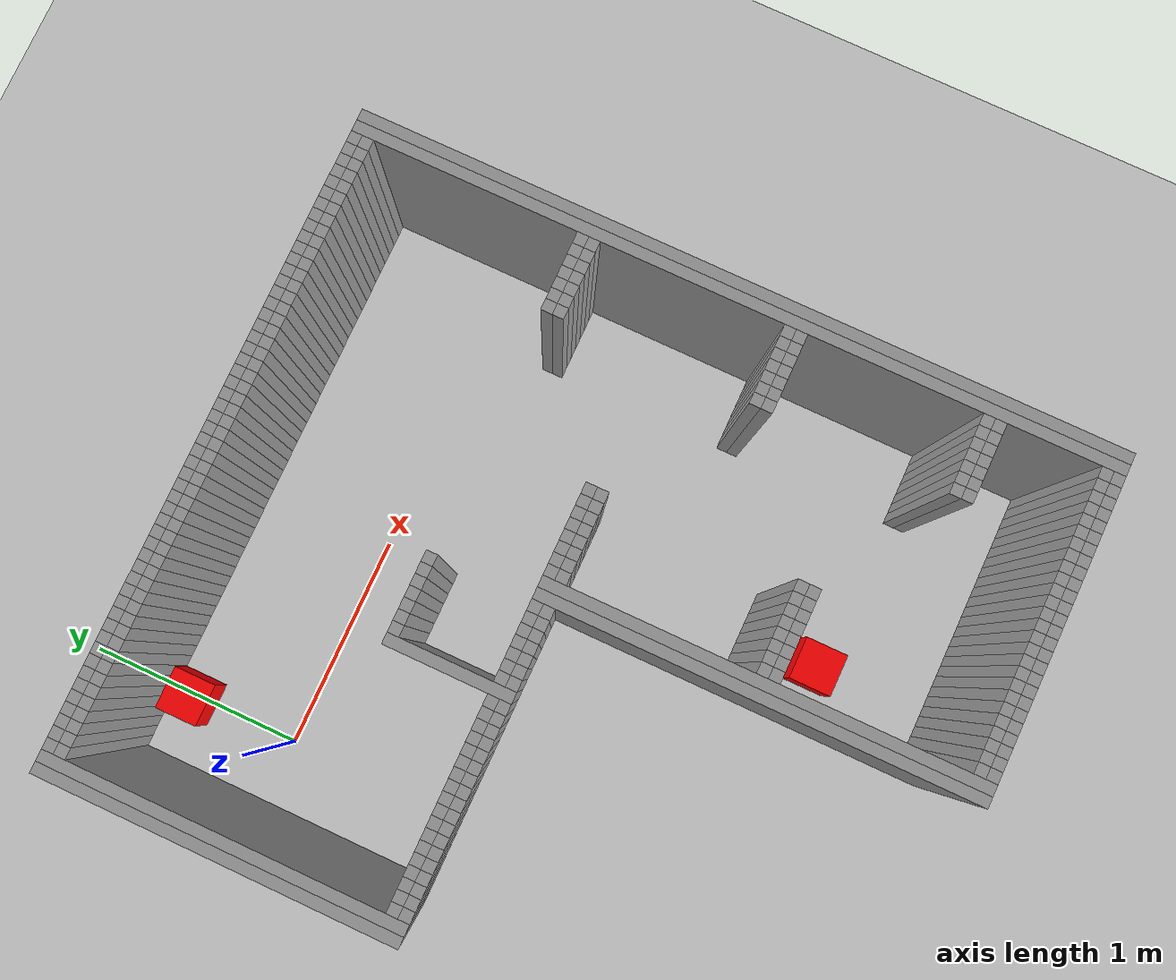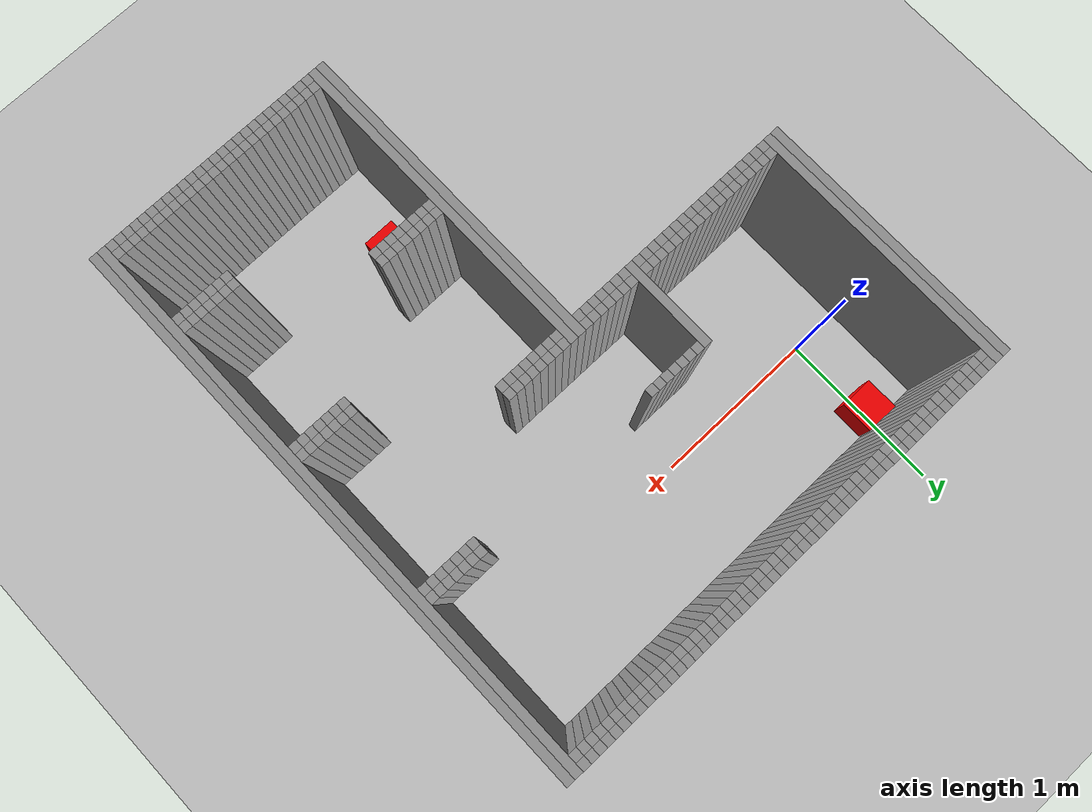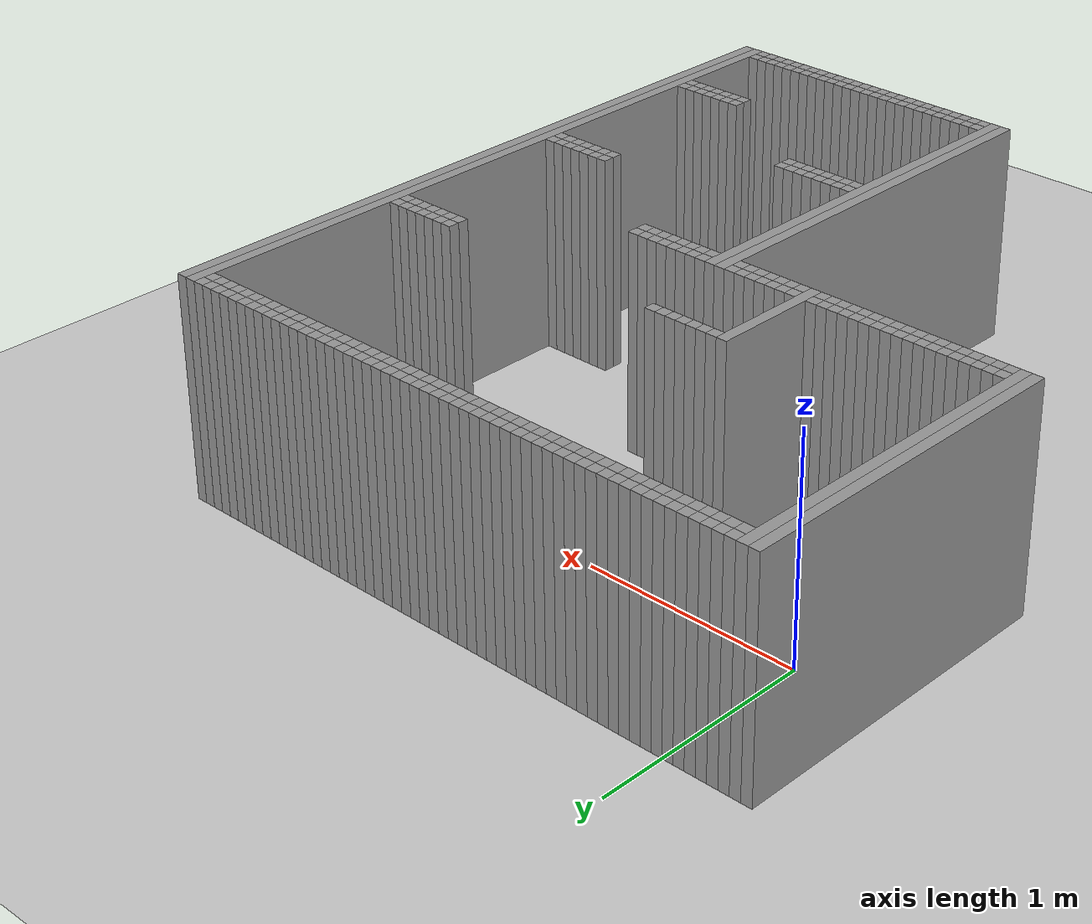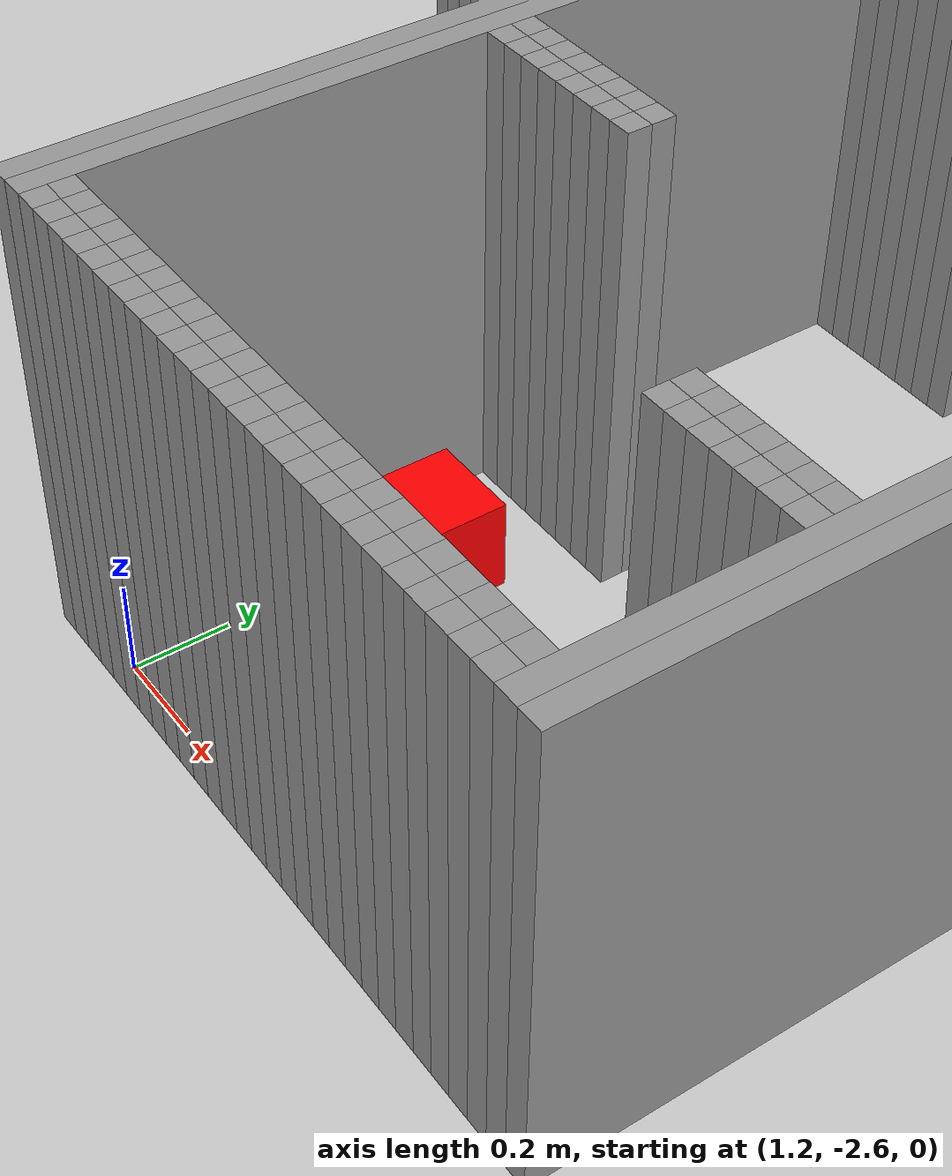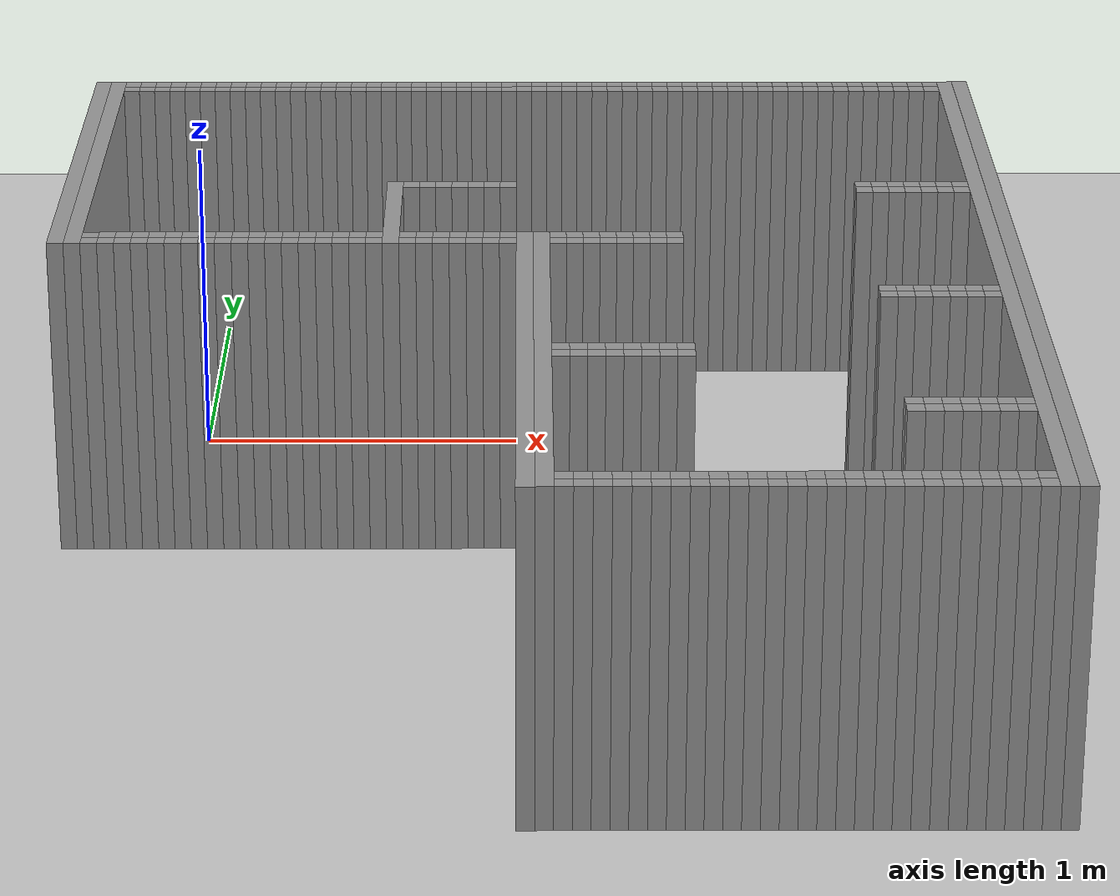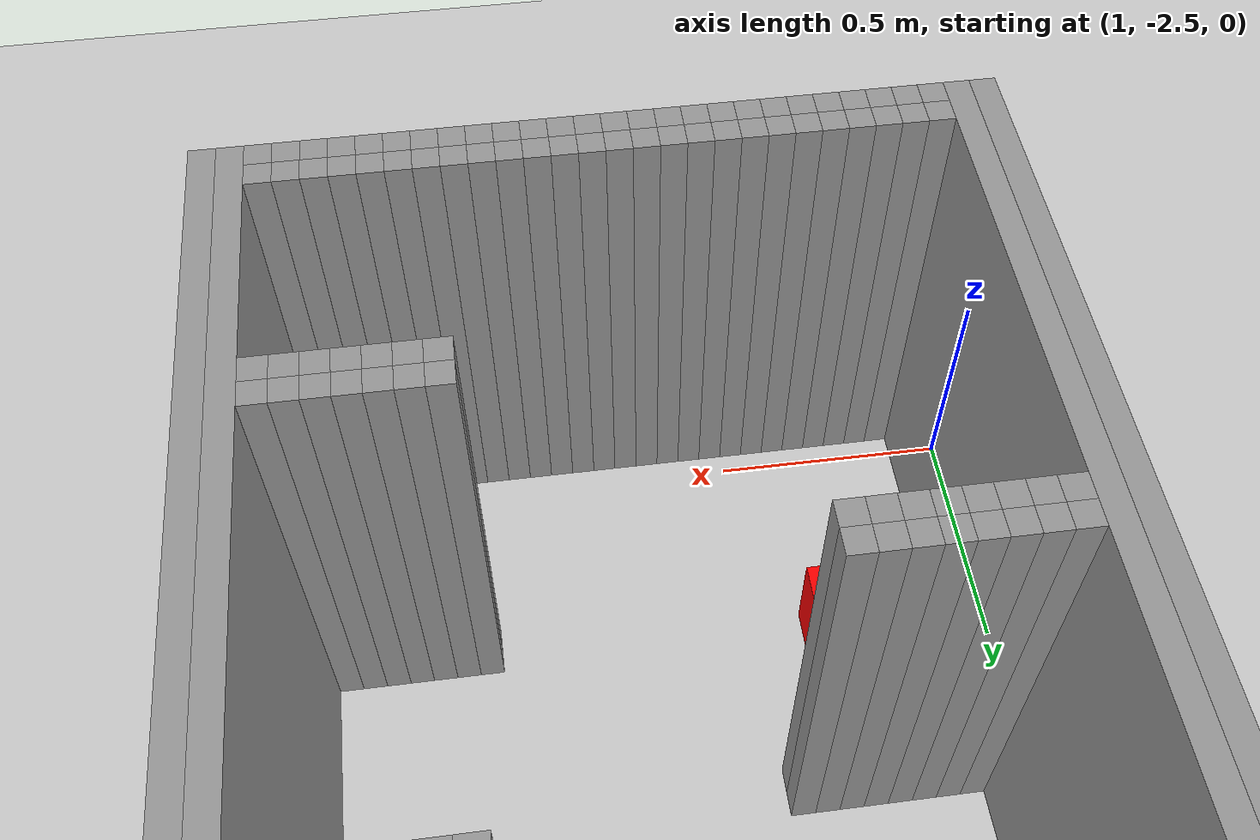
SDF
<?xml version="1.0" ?>
<sdf version="1.6">
  <world name="default">
    <plugin name="gazebo_ros_init" filename="libgazebo_ros_init.so"/>
    <plugin name="gazebo_ros_factory" filename="libgazebo_ros_factory.so"/>
    <plugin name="gazebo_ros_state" filename="libgazebo_ros_state.so"/>

    <!-- 插入默认地面 -->
    <include>
      <uri>model://ground_plane</uri>
    </include>

    <!-- 插入一个光源 -->
    <include>
      <uri>model://sun</uri>
    </include>

    <!-- 插入你生成的墙体 -->
    <include>
      <uri>file:///home/suda/drone_ugv_ws/src/map_struct/models/auto_walls</uri>
    </include>

    <!-- 红色小立方体 -->
    <model name="red_cube_1">
      <pose>0 0.5 0.1 0 0 0</pose>  <!-- z=0.1（高度的一半），确保底部贴地 -->
      <link name="link">
      <kinematic>true</kinematic>
        <collision name="collision">
          <geometry>
            <box>
              <size>0.2 0.2 0.2</size>  <!-- 0.2m长宽高 -->
            </box>
          </geometry>
        </collision>
        <visual name="visual">
          <geometry>
            <box>
              <size>0.2 0.2 0.2</size>  <!-- 视觉尺寸与碰撞尺寸一致 -->
            </box>
          </geometry>
          <material>
            <ambient>1 0 0 1</ambient>   <!-- 红色环境光 -->
            <diffuse>1 0 0 1</diffuse>   <!-- 红色漫反射 -->
            <specular>0.2 0.2 0.2 1</specular>  <!-- 轻微高光 -->
          </material>
        </visual>
        <inertial>
          <mass>0.02</mass>  <!-- 小质量适配小尺寸 -->
          <inertia>
            <!-- 0.2m边长立方体的转动惯量计算：(mass * (a² + b²)) / 12 -->
            <ixx>0.000013</ixx>
            <ixy>0</ixy>
            <ixz>0</ixz>
            <iyy>0.000013</iyy>
            <iyz>0</iyz>
            <izz>0.000013</izz>
          </inertia>
        </inertial>
      </link>
    </model>

    <model name="red_cube_2">
      <pose>1.3 -2.0 0.1 0 0 0</pose>  <!-- z=0.1（高度的一半），确保底部贴地 -->
      <link name="link">
      <kinematic>true</kinematic>
        <collision name="collision">
          <geometry>
            <box>
              <size>0.2 0.2 0.2</size>  <!-- 0.2m长宽高 -->
            </box>
          </geometry>
        </collision>
        <visual name="visual">
          <geometry>
            <box>
              <size>0.2 0.2 0.2</size>  <!-- 视觉尺寸与碰撞尺寸一致 -->
            </box>
          </geometry>
          <material>
            <ambient>1 0 0 1</ambient>   <!-- 红色环境光 -->
            <diffuse>1 0 0 1</diffuse>   <!-- 红色漫反射 -->
            <specular>0.2 0.2 0.2 1</specular>  <!-- 轻微高光 -->
          </material>
        </visual>
        <inertial>
          <mass>0.02</mass>  <!-- 小质量适配小尺寸 -->
          <inertia>
            <!-- 0.2m边长立方体的转动惯量计算：(mass * (a² + b²)) / 12 -->
            <ixx>0.000013</ixx>
            <ixy>0</ixy>
            <ixz>0</ixz>
            <iyy>0.000013</iyy>
            <iyz>0</iyz>
            <izz>0.000013</izz>
          </inertia>
        </inertial>
      </link>
    </model>

  </world>
</sdf>

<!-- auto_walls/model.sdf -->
<sdf version="1.6">
  <model name="optimized_walls">

    <link name="wall_large_0">
      <pose>-0.3710 -0.0700 0.5000 0 0 0</pose>
      <collision name="collision">
        <geometry><box><size>0.0500 1.5500 1.0</size></box></geometry>
      </collision>
      <visual name="visual">
        <geometry><box><size>0.0500 1.5500 1.0</size></box></geometry>
        <material><script><name>Gazebo/Grey</name></script></material>
      </visual>
    </link>

    <link name="wall_large_1">
      <pose>-0.3210 -0.0700 0.5000 0 0 0</pose>
      <collision name="collision">
        <geometry><box><size>0.0500 1.5500 1.0</size></box></geometry>
      </collision>
      <visual name="visual">
        <geometry><box><size>0.0500 1.5500 1.0</size></box></geometry>
        <material><script><name>Gazebo/Grey</name></script></material>
      </visual>
    </link>

    <link name="wall_small_2_0">
      <pose>-0.2710 0.6800 0.5000 0 0 0</pose>
      <collision name="collision">
        <geometry><box><size>0.05 0.05 1.0</size></box></geometry>
      </collision>
      <visual name="visual">
        <geometry><box><size>0.05 0.05 1.0</size></box></geometry>
        <material><script><name>Gazebo/Grey</name></script></material>
      </visual>
    </link>

    <link name="wall_small_2_1">
      <pose>-0.2710 0.6300 0.5000 0 0 0</pose>
      <collision name="collision">
        <geometry><box><size>0.05 0.05 1.0</size></box></geometry>
      </collision>
      <visual name="visual">
        <geometry><box><size>0.05 0.05 1.0</size></box></geometry>
        <material><script><name>Gazebo/Grey</name></script></material>
      </visual>
    </link>

    <link name="wall_small_3_0">
      <pose>-0.2710 -0.7700 0.5000 0 0 0</pose>
      <collision name="collision">
        <geometry><box><size>0.05 0.05 1.0</size></box></geometry>
      </collision>
      <visual name="visual">
        <geometry><box><size>0.05 0.05 1.0</size></box></geometry>
        <material><script><name>Gazebo/Grey</name></script></material>
      </visual>
    </link>

    <link name="wall_small_3_1">
      <pose>-0.2710 -0.8200 0.5000 0 0 0</pose>
      <collision name="collision">
        <geometry><box><size>0.05 0.05 1.0</size></box></geometry>
      </collision>
      <visual name="visual">
        <geometry><box><size>0.05 0.05 1.0</size></box></geometry>
        <material><script><name>Gazebo/Grey</name></script></material>
      </visual>
    </link>

    <link name="wall_small_4_0">
      <pose>-0.2210 0.6800 0.5000 0 0 0</pose>
      <collision name="collision">
        <geometry><box><size>0.05 0.05 1.0</size></box></geometry>
      </collision>
      <visual name="visual">
        <geometry><box><size>0.05 0.05 1.0</size></box></geometry>
        <material><script><name>Gazebo/Grey</name></script></material>
      </visual>
    </link>

    <link name="wall_small_4_1">
      <pose>-0.2210 0.6300 0.5000 0 0 0</pose>
      <collision name="collision">
        <geometry><box><size>0.05 0.05 1.0</size></box></geometry>
      </collision>
      <visual name="visual">
        <geometry><box><size>0.05 0.05 1.0</size></box></geometry>
        <material><script><name>Gazebo/Grey</name></script></material>
      </visual>
    </link>

    <link name="wall_small_5_0">
      <pose>-0.2210 -0.7700 0.5000 0 0 0</pose>
      <collision name="collision">
        <geometry><box><size>0.05 0.05 1.0</size></box></geometry>
      </collision>
      <visual name="visual">
        <geometry><box><size>0.05 0.05 1.0</size></box></geometry>
        <material><script><name>Gazebo/Grey</name></script></material>
      </visual>
    </link>

    <link name="wall_small_5_1">
      <pose>-0.2210 -0.8200 0.5000 0 0 0</pose>
      <collision name="collision">
        <geometry><box><size>0.05 0.05 1.0</size></box></geometry>
      </collision>
      <visual name="visual">
        <geometry><box><size>0.05 0.05 1.0</size></box></geometry>
        <material><script><name>Gazebo/Grey</name></script></material>
      </visual>
    </link>

    <link name="wall_small_6_0">
      <pose>-0.1710 0.6800 0.5000 0 0 0</pose>
      <collision name="collision">
        <geometry><box><size>0.05 0.05 1.0</size></box></geometry>
      </collision>
      <visual name="visual">
        <geometry><box><size>0.05 0.05 1.0</size></box></geometry>
        <material><script><name>Gazebo/Grey</name></script></material>
      </visual>
    </link>

    <link name="wall_small_6_1">
      <pose>-0.1710 0.6300 0.5000 0 0 0</pose>
      <collision name="collision">
        <geometry><box><size>0.05 0.05 1.0</size></box></geometry>
      </collision>
      <visual name="visual">
        <geometry><box><size>0.05 0.05 1.0</size></box></geometry>
        <material><script><name>Gazebo/Grey</name></script></material>
      </visual>
    </link>

    <link name="wall_small_7_0">
      <pose>-0.1710 -0.7700 0.5000 0 0 0</pose>
      <collision name="collision">
        <geometry><box><size>0.05 0.05 1.0</size></box></geometry>
      </collision>
      <visual name="visual">
        <geometry><box><size>0.05 0.05 1.0</size></box></geometry>
        <material><script><name>Gazebo/Grey</name></script></material>
      </visual>
    </link>

    <link name="wall_small_7_1">
      <pose>-0.1710 -0.8200 0.5000 0 0 0</pose>
      <collision name="collision">
        <geometry><box><size>0.05 0.05 1.0</size></box></geometry>
      </collision>
      <visual name="visual">
        <geometry><box><size>0.05 0.05 1.0</size></box></geometry>
        <material><script><name>Gazebo/Grey</name></script></material>
      </visual>
    </link>

    <link name="wall_small_8_0">
      <pose>-0.1210 0.6800 0.5000 0 0 0</pose>
      <collision name="collision">
        <geometry><box><size>0.05 0.05 1.0</size></box></geometry>
      </collision>
      <visual name="visual">
        <geometry><box><size>0.05 0.05 1.0</size></box></geometry>
        <material><script><name>Gazebo/Grey</name></script></material>
      </visual>
    </link>

    <link name="wall_small_8_1">
      <pose>-0.1210 0.6300 0.5000 0 0 0</pose>
      <collision name="collision">
        <geometry><box><size>0.05 0.05 1.0</size></box></geometry>
      </collision>
      <visual name="visual">
        <geometry><box><size>0.05 0.05 1.0</size></box></geometry>
        <material><script><name>Gazebo/Grey</name></script></material>
      </visual>
    </link>

    <link name="wall_small_9_0">
      <pose>-0.1210 -0.7700 0.5000 0 0 0</pose>
      <collision name="collision">
        <geometry><box><size>0.05 0.05 1.0</size></box></geometry>
      </collision>
      <visual name="visual">
        <geometry><box><size>0.05 0.05 1.0</size></box></geometry>
        <material><script><name>Gazebo/Grey</name></script></material>
      </visual>
    </link>

    <link name="wall_small_9_1">
      <pose>-0.1210 -0.8200 0.5000 0 0 0</pose>
      <collision name="collision">
        <geometry><box><size>0.05 0.05 1.0</size></box></geometry>
      </collision>
      <visual name="visual">
        <geometry><box><size>0.05 0.05 1.0</size></box></geometry>
        <material><script><name>Gazebo/Grey</name></script></material>
      </visual>
    </link>

    <link name="wall_small_10_0">
      <pose>-0.0710 0.6800 0.5000 0 0 0</pose>
      <collision name="collision">
        <geometry><box><size>0.05 0.05 1.0</size></box></geometry>
      </collision>
      <visual name="visual">
        <geometry><box><size>0.05 0.05 1.0</size></box></geometry>
        <material><script><name>Gazebo/Grey</name></script></material>
      </visual>
    </link>

    <link name="wall_small_10_1">
      <pose>-0.0710 0.6300 0.5000 0 0 0</pose>
      <collision name="collision">
        <geometry><box><size>0.05 0.05 1.0</size></box></geometry>
      </collision>
      <visual name="visual">
        <geometry><box><size>0.05 0.05 1.0</size></box></geometry>
        <material><script><name>Gazebo/Grey</name></script></material>
      </visual>
    </link>

    <link name="wall_small_11_0">
      <pose>-0.0710 -0.7700 0.5000 0 0 0</pose>
      <collision name="collision">
        <geometry><box><size>0.05 0.05 1.0</size></box></geometry>
      </collision>
      <visual name="visual">
        <geometry><box><size>0.05 0.05 1.0</size></box></geometry>
        <material><script><name>Gazebo/Grey</name></script></material>
      </visual>
    </link>

    <link name="wall_small_11_1">
      <pose>-0.0710 -0.8200 0.5000 0 0 0</pose>
      <collision name="collision">
        <geometry><box><size>0.05 0.05 1.0</size></box></geometry>
      </collision>
      <visual name="visual">
        <geometry><box><size>0.05 0.05 1.0</size></box></geometry>
        <material><script><name>Gazebo/Grey</name></script></material>
      </visual>
    </link>

    <link name="wall_small_12_0">
      <pose>-0.0210 0.6800 0.5000 0 0 0</pose>
      <collision name="collision">
        <geometry><box><size>0.05 0.05 1.0</size></box></geometry>
      </collision>
      <visual name="visual">
        <geometry><box><size>0.05 0.05 1.0</size></box></geometry>
        <material><script><name>Gazebo/Grey</name></script></material>
      </visual>
    </link>

    <link name="wall_small_12_1">
      <pose>-0.0210 0.6300 0.5000 0 0 0</pose>
      <collision name="collision">
        <geometry><box><size>0.05 0.05 1.0</size></box></geometry>
      </collision>
      <visual name="visual">
        <geometry><box><size>0.05 0.05 1.0</size></box></geometry>
        <material><script><name>Gazebo/Grey</name></script></material>
      </visual>
    </link>

    <link name="wall_small_13_0">
      <pose>-0.0210 -0.7700 0.5000 0 0 0</pose>
      <collision name="collision">
        <geometry><box><size>0.05 0.05 1.0</size></box></geometry>
      </collision>
      <visual name="visual">
        <geometry><box><size>0.05 0.05 1.0</size></box></geometry>
        <material><script><name>Gazebo/Grey</name></script></material>
      </visual>
    </link>

    <link name="wall_small_13_1">
      <pose>-0.0210 -0.8200 0.5000 0 0 0</pose>
      <collision name="collision">
        <geometry><box><size>0.05 0.05 1.0</size></box></geometry>
      </collision>
      <visual name="visual">
        <geometry><box><size>0.05 0.05 1.0</size></box></geometry>
        <material><script><name>Gazebo/Grey</name></script></material>
      </visual>
    </link>

    <link name="wall_small_14_0">
      <pose>0.0290 0.6800 0.5000 0 0 0</pose>
      <collision name="collision">
        <geometry><box><size>0.05 0.05 1.0</size></box></geometry>
      </collision>
      <visual name="visual">
        <geometry><box><size>0.05 0.05 1.0</size></box></geometry>
        <material><script><name>Gazebo/Grey</name></script></material>
      </visual>
    </link>

    <link name="wall_small_14_1">
      <pose>0.0290 0.6300 0.5000 0 0 0</pose>
      <collision name="collision">
        <geometry><box><size>0.05 0.05 1.0</size></box></geometry>
      </collision>
      <visual name="visual">
        <geometry><box><size>0.05 0.05 1.0</size></box></geometry>
        <material><script><name>Gazebo/Grey</name></script></material>
      </visual>
    </link>

    <link name="wall_small_15_0">
      <pose>0.0290 -0.7700 0.5000 0 0 0</pose>
      <collision name="collision">
        <geometry><box><size>0.05 0.05 1.0</size></box></geometry>
      </collision>
      <visual name="visual">
        <geometry><box><size>0.05 0.05 1.0</size></box></geometry>
        <material><script><name>Gazebo/Grey</name></script></material>
      </visual>
    </link>

    <link name="wall_small_15_1">
      <pose>0.0290 -0.8200 0.5000 0 0 0</pose>
      <collision name="collision">
        <geometry><box><size>0.05 0.05 1.0</size></box></geometry>
      </collision>
      <visual name="visual">
        <geometry><box><size>0.05 0.05 1.0</size></box></geometry>
        <material><script><name>Gazebo/Grey</name></script></material>
      </visual>
    </link>

    <link name="wall_small_16_0">
      <pose>0.0790 0.6800 0.5000 0 0 0</pose>
      <collision name="collision">
        <geometry><box><size>0.05 0.05 1.0</size></box></geometry>
      </collision>
      <visual name="visual">
        <geometry><box><size>0.05 0.05 1.0</size></box></geometry>
        <material><script><name>Gazebo/Grey</name></script></material>
      </visual>
    </link>

    <link name="wall_small_16_1">
      <pose>0.0790 0.6300 0.5000 0 0 0</pose>
      <collision name="collision">
        <geometry><box><size>0.05 0.05 1.0</size></box></geometry>
      </collision>
      <visual name="visual">
        <geometry><box><size>0.05 0.05 1.0</size></box></geometry>
        <material><script><name>Gazebo/Grey</name></script></material>
      </visual>
    </link>

    <link name="wall_small_17_0">
      <pose>0.0790 -0.7700 0.5000 0 0 0</pose>
      <collision name="collision">
        <geometry><box><size>0.05 0.05 1.0</size></box></geometry>
      </collision>
      <visual name="visual">
        <geometry><box><size>0.05 0.05 1.0</size></box></geometry>
        <material><script><name>Gazebo/Grey</name></script></material>
      </visual>
    </link>

    <link name="wall_small_17_1">
      <pose>0.0790 -0.8200 0.5000 0 0 0</pose>
      <collision name="collision">
        <geometry><box><size>0.05 0.05 1.0</size></box></geometry>
      </collision>
      <visual name="visual">
        <geometry><box><size>0.05 0.05 1.0</size></box></geometry>
        <material><script><name>Gazebo/Grey</name></script></material>
      </visual>
    </link>

    <link name="wall_small_18_0">
      <pose>0.1290 0.6800 0.5000 0 0 0</pose>
      <collision name="collision">
        <geometry><box><size>0.05 0.05 1.0</size></box></geometry>
      </collision>
      <visual name="visual">
        <geometry><box><size>0.05 0.05 1.0</size></box></geometry>
        <material><script><name>Gazebo/Grey</name></script></material>
      </visual>
    </link>

    <link name="wall_small_18_1">
      <pose>0.1290 0.6300 0.5000 0 0 0</pose>
      <collision name="collision">
        <geometry><box><size>0.05 0.05 1.0</size></box></geometry>
      </collision>
      <visual name="visual">
        <geometry><box><size>0.05 0.05 1.0</size></box></geometry>
        <material><script><name>Gazebo/Grey</name></script></material>
      </visual>
    </link>

    <link name="wall_small_19_0">
      <pose>0.1290 -0.7700 0.5000 0 0 0</pose>
      <collision name="collision">
        <geometry><box><size>0.05 0.05 1.0</size></box></geometry>
      </collision>
      <visual name="visual">
        <geometry><box><size>0.05 0.05 1.0</size></box></geometry>
        <material><script><name>Gazebo/Grey</name></script></material>
      </visual>
    </link>

    <link name="wall_small_19_1">
      <pose>0.1290 -0.8200 0.5000 0 0 0</pose>
      <collision name="collision">
        <geometry><box><size>0.05 0.05 1.0</size></box></geometry>
      </collision>
      <visual name="visual">
        <geometry><box><size>0.05 0.05 1.0</size></box></geometry>
        <material><script><name>Gazebo/Grey</name></script></material>
      </visual>
    </link>

    <link name="wall_small_20_0">
      <pose>0.1790 0.6800 0.5000 0 0 0</pose>
      <collision name="collision">
        <geometry><box><size>0.05 0.05 1.0</size></box></geometry>
      </collision>
      <visual name="visual">
        <geometry><box><size>0.05 0.05 1.0</size></box></geometry>
        <material><script><name>Gazebo/Grey</name></script></material>
      </visual>
    </link>

    <link name="wall_small_20_1">
      <pose>0.1790 0.6300 0.5000 0 0 0</pose>
      <collision name="collision">
        <geometry><box><size>0.05 0.05 1.0</size></box></geometry>
      </collision>
      <visual name="visual">
        <geometry><box><size>0.05 0.05 1.0</size></box></geometry>
        <material><script><name>Gazebo/Grey</name></script></material>
      </visual>
    </link>

    <link name="wall_small_21_0">
      <pose>0.1790 -0.7700 0.5000 0 0 0</pose>
      <collision name="collision">
        <geometry><box><size>0.05 0.05 1.0</size></box></geometry>
      </collision>
      <visual name="visual">
        <geometry><box><size>0.05 0.05 1.0</size></box></geometry>
        <material><script><name>Gazebo/Grey</name></script></material>
      </visual>
    </link>

    <link name="wall_small_21_1">
      <pose>0.1790 -0.8200 0.5000 0 0 0</pose>
      <collision name="collision">
        <geometry><box><size>0.05 0.05 1.0</size></box></geometry>
      </collision>
      <visual name="visual">
        <geometry><box><size>0.05 0.05 1.0</size></box></geometry>
        <material><script><name>Gazebo/Grey</name></script></material>
      </visual>
    </link>

    <link name="wall_small_22_0">
      <pose>0.2290 0.6800 0.5000 0 0 0</pose>
      <collision name="collision">
        <geometry><box><size>0.05 0.05 1.0</size></box></geometry>
      </collision>
      <visual name="visual">
        <geometry><box><size>0.05 0.05 1.0</size></box></geometry>
        <material><script><name>Gazebo/Grey</name></script></material>
      </visual>
    </link>

    <link name="wall_small_22_1">
      <pose>0.2290 0.6300 0.5000 0 0 0</pose>
      <collision name="collision">
        <geometry><box><size>0.05 0.05 1.0</size></box></geometry>
      </collision>
      <visual name="visual">
        <geometry><box><size>0.05 0.05 1.0</size></box></geometry>
        <material><script><name>Gazebo/Grey</name></script></material>
      </visual>
    </link>

    <link name="wall_small_23_0">
      <pose>0.2290 -0.7700 0.5000 0 0 0</pose>
      <collision name="collision">
        <geometry><box><size>0.05 0.05 1.0</size></box></geometry>
      </collision>
      <visual name="visual">
        <geometry><box><size>0.05 0.05 1.0</size></box></geometry>
        <material><script><name>Gazebo/Grey</name></script></material>
      </visual>
    </link>

    <link name="wall_small_23_1">
      <pose>0.2290 -0.8200 0.5000 0 0 0</pose>
      <collision name="collision">
        <geometry><box><size>0.05 0.05 1.0</size></box></geometry>
      </collision>
      <visual name="visual">
        <geometry><box><size>0.05 0.05 1.0</size></box></geometry>
        <material><script><name>Gazebo/Grey</name></script></material>
      </visual>
    </link>

    <link name="wall_small_24_0">
      <pose>0.2790 0.6800 0.5000 0 0 0</pose>
      <collision name="collision">
        <geometry><box><size>0.05 0.05 1.0</size></box></geometry>
      </collision>
      <visual name="visual">
        <geometry><box><size>0.05 0.05 1.0</size></box></geometry>
        <material><script><name>Gazebo/Grey</name></script></material>
      </visual>
    </link>

    <link name="wall_small_24_1">
      <pose>0.2790 0.6300 0.5000 0 0 0</pose>
      <collision name="collision">
        <geometry><box><size>0.05 0.05 1.0</size></box></geometry>
      </collision>
      <visual name="visual">
        <geometry><box><size>0.05 0.05 1.0</size></box></geometry>
        <material><script><name>Gazebo/Grey</name></script></material>
      </visual>
    </link>

    <link name="wall_small_25_0">
      <pose>0.2790 -0.7700 0.5000 0 0 0</pose>
      <collision name="collision">
        <geometry><box><size>0.05 0.05 1.0</size></box></geometry>
      </collision>
      <visual name="visual">
        <geometry><box><size>0.05 0.05 1.0</size></box></geometry>
        <material><script><name>Gazebo/Grey</name></script></material>
      </visual>
    </link>

    <link name="wall_small_25_1">
      <pose>0.2790 -0.8200 0.5000 0 0 0</pose>
      <collision name="collision">
        <geometry><box><size>0.05 0.05 1.0</size></box></geometry>
      </collision>
      <visual name="visual">
        <geometry><box><size>0.05 0.05 1.0</size></box></geometry>
        <material><script><name>Gazebo/Grey</name></script></material>
      </visual>
    </link>

    <link name="wall_small_26_0">
      <pose>0.3290 0.6800 0.5000 0 0 0</pose>
      <collision name="collision">
        <geometry><box><size>0.05 0.05 1.0</size></box></geometry>
      </collision>
      <visual name="visual">
        <geometry><box><size>0.05 0.05 1.0</size></box></geometry>
        <material><script><name>Gazebo/Grey</name></script></material>
      </visual>
    </link>

    <link name="wall_small_26_1">
      <pose>0.3290 0.6300 0.5000 0 0 0</pose>
      <collision name="collision">
        <geometry><box><size>0.05 0.05 1.0</size></box></geometry>
      </collision>
      <visual name="visual">
        <geometry><box><size>0.05 0.05 1.0</size></box></geometry>
        <material><script><name>Gazebo/Grey</name></script></material>
      </visual>
    </link>

    <link name="wall_small_27_0">
      <pose>0.3290 -0.7700 0.5000 0 0 0</pose>
      <collision name="collision">
        <geometry><box><size>0.05 0.05 1.0</size></box></geometry>
      </collision>
      <visual name="visual">
        <geometry><box><size>0.05 0.05 1.0</size></box></geometry>
        <material><script><name>Gazebo/Grey</name></script></material>
      </visual>
    </link>

    <link name="wall_small_27_1">
      <pose>0.3290 -0.8200 0.5000 0 0 0</pose>
      <collision name="collision">
        <geometry><box><size>0.05 0.05 1.0</size></box></geometry>
      </collision>
      <visual name="visual">
        <geometry><box><size>0.05 0.05 1.0</size></box></geometry>
        <material><script><name>Gazebo/Grey</name></script></material>
      </visual>
    </link>

    <link name="wall_small_28_0">
      <pose>0.3790 0.6800 0.5000 0 0 0</pose>
      <collision name="collision">
        <geometry><box><size>0.05 0.05 1.0</size></box></geometry>
      </collision>
      <visual name="visual">
        <geometry><box><size>0.05 0.05 1.0</size></box></geometry>
        <material><script><name>Gazebo/Grey</name></script></material>
      </visual>
    </link>

    <link name="wall_small_28_1">
      <pose>0.3790 0.6300 0.5000 0 0 0</pose>
      <collision name="collision">
        <geometry><box><size>0.05 0.05 1.0</size></box></geometry>
      </collision>
      <visual name="visual">
        <geometry><box><size>0.05 0.05 1.0</size></box></geometry>
        <material><script><name>Gazebo/Grey</name></script></material>
      </visual>
    </link>

    <link name="wall_small_29_0">
      <pose>0.3790 -0.7700 0.5000 0 0 0</pose>
      <collision name="collision">
        <geometry><box><size>0.05 0.05 1.0</size></box></geometry>
      </collision>
      <visual name="visual">
        <geometry><box><size>0.05 0.05 1.0</size></box></geometry>
        <material><script><name>Gazebo/Grey</name></script></material>
      </visual>
    </link>

    <link name="wall_small_29_1">
      <pose>0.3790 -0.8200 0.5000 0 0 0</pose>
      <collision name="collision">
        <geometry><box><size>0.05 0.05 1.0</size></box></geometry>
      </collision>
      <visual name="visual">
        <geometry><box><size>0.05 0.05 1.0</size></box></geometry>
        <material><script><name>Gazebo/Grey</name></script></material>
      </visual>
    </link>

    <link name="wall_small_30_0">
      <pose>0.4290 0.6800 0.5000 0 0 0</pose>
      <collision name="collision">
        <geometry><box><size>0.05 0.05 1.0</size></box></geometry>
      </collision>
      <visual name="visual">
        <geometry><box><size>0.05 0.05 1.0</size></box></geometry>
        <material><script><name>Gazebo/Grey</name></script></material>
      </visual>
    </link>

    <link name="wall_small_30_1">
      <pose>0.4290 0.6300 0.5000 0 0 0</pose>
      <collision name="collision">
        <geometry><box><size>0.05 0.05 1.0</size></box></geometry>
      </collision>
      <visual name="visual">
        <geometry><box><size>0.05 0.05 1.0</size></box></geometry>
        <material><script><name>Gazebo/Grey</name></script></material>
      </visual>
    </link>

    <link name="wall_small_31_0">
      <pose>0.4290 -0.7700 0.5000 0 0 0</pose>
      <collision name="collision">
        <geometry><box><size>0.05 0.05 1.0</size></box></geometry>
      </collision>
      <visual name="visual">
        <geometry><box><size>0.05 0.05 1.0</size></box></geometry>
        <material><script><name>Gazebo/Grey</name></script></material>
      </visual>
    </link>

    <link name="wall_small_31_1">
      <pose>0.4290 -0.8200 0.5000 0 0 0</pose>
      <collision name="collision">
        <geometry><box><size>0.05 0.05 1.0</size></box></geometry>
      </collision>
      <visual name="visual">
        <geometry><box><size>0.05 0.05 1.0</size></box></geometry>
        <material><script><name>Gazebo/Grey</name></script></material>
      </visual>
    </link>

    <link name="wall_small_32_0">
      <pose>0.4790 0.6800 0.5000 0 0 0</pose>
      <collision name="collision">
        <geometry><box><size>0.05 0.05 1.0</size></box></geometry>
      </collision>
      <visual name="visual">
        <geometry><box><size>0.05 0.05 1.0</size></box></geometry>
        <material><script><name>Gazebo/Grey</name></script></material>
      </visual>
    </link>

    <link name="wall_small_32_1">
      <pose>0.4790 0.6300 0.5000 0 0 0</pose>
      <collision name="collision">
        <geometry><box><size>0.05 0.05 1.0</size></box></geometry>
      </collision>
      <visual name="visual">
        <geometry><box><size>0.05 0.05 1.0</size></box></geometry>
        <material><script><name>Gazebo/Grey</name></script></material>
      </visual>
    </link>

    <link name="wall_small_33_0">
      <pose>0.4790 -0.7700 0.5000 0 0 0</pose>
      <collision name="collision">
        <geometry><box><size>0.05 0.05 1.0</size></box></geometry>
      </collision>
      <visual name="visual">
        <geometry><box><size>0.05 0.05 1.0</size></box></geometry>
        <material><script><name>Gazebo/Grey</name></script></material>
      </visual>
    </link>

    <link name="wall_small_33_1">
      <pose>0.4790 -0.8200 0.5000 0 0 0</pose>
      <collision name="collision">
        <geometry><box><size>0.05 0.05 1.0</size></box></geometry>
      </collision>
      <visual name="visual">
        <geometry><box><size>0.05 0.05 1.0</size></box></geometry>
        <material><script><name>Gazebo/Grey</name></script></material>
      </visual>
    </link>

    <link name="wall_small_34_0">
      <pose>0.5290 0.6800 0.5000 0 0 0</pose>
      <collision name="collision">
        <geometry><box><size>0.05 0.05 1.0</size></box></geometry>
      </collision>
      <visual name="visual">
        <geometry><box><size>0.05 0.05 1.0</size></box></geometry>
        <material><script><name>Gazebo/Grey</name></script></material>
      </visual>
    </link>

    <link name="wall_small_34_1">
      <pose>0.5290 0.6300 0.5000 0 0 0</pose>
      <collision name="collision">
        <geometry><box><size>0.05 0.05 1.0</size></box></geometry>
      </collision>
      <visual name="visual">
        <geometry><box><size>0.05 0.05 1.0</size></box></geometry>
        <material><script><name>Gazebo/Grey</name></script></material>
      </visual>
    </link>

    <link name="wall_small_35_0">
      <pose>0.5290 -0.7700 0.5000 0 0 0</pose>
      <collision name="collision">
        <geometry><box><size>0.05 0.05 1.0</size></box></geometry>
      </collision>
      <visual name="visual">
        <geometry><box><size>0.05 0.05 1.0</size></box></geometry>
        <material><script><name>Gazebo/Grey</name></script></material>
      </visual>
    </link>

    <link name="wall_small_35_1">
      <pose>0.5290 -0.8200 0.5000 0 0 0</pose>
      <collision name="collision">
        <geometry><box><size>0.05 0.05 1.0</size></box></geometry>
      </collision>
      <visual name="visual">
        <geometry><box><size>0.05 0.05 1.0</size></box></geometry>
        <material><script><name>Gazebo/Grey</name></script></material>
      </visual>
    </link>

    <link name="wall_small_36_0">
      <pose>0.5790 0.6800 0.5000 0 0 0</pose>
      <collision name="collision">
        <geometry><box><size>0.05 0.05 1.0</size></box></geometry>
      </collision>
      <visual name="visual">
        <geometry><box><size>0.05 0.05 1.0</size></box></geometry>
        <material><script><name>Gazebo/Grey</name></script></material>
      </visual>
    </link>

    <link name="wall_small_36_1">
      <pose>0.5790 0.6300 0.5000 0 0 0</pose>
      <collision name="collision">
        <geometry><box><size>0.05 0.05 1.0</size></box></geometry>
      </collision>
      <visual name="visual">
        <geometry><box><size>0.05 0.05 1.0</size></box></geometry>
        <material><script><name>Gazebo/Grey</name></script></material>
      </visual>
    </link>

    <link name="wall_small_37_0">
      <pose>0.5790 -0.7700 0.5000 0 0 0</pose>
      <collision name="collision">
        <geometry><box><size>0.05 0.05 1.0</size></box></geometry>
      </collision>
      <visual name="visual">
        <geometry><box><size>0.05 0.05 1.0</size></box></geometry>
        <material><script><name>Gazebo/Grey</name></script></material>
      </visual>
    </link>

    <link name="wall_small_37_1">
      <pose>0.5790 -0.8200 0.5000 0 0 0</pose>
      <collision name="collision">
        <geometry><box><size>0.05 0.05 1.0</size></box></geometry>
      </collision>
      <visual name="visual">
        <geometry><box><size>0.05 0.05 1.0</size></box></geometry>
        <material><script><name>Gazebo/Grey</name></script></material>
      </visual>
    </link>

    <link name="wall_small_38_0">
      <pose>0.6290 0.6800 0.5000 0 0 0</pose>
      <collision name="collision">
        <geometry><box><size>0.05 0.05 1.0</size></box></geometry>
      </collision>
      <visual name="visual">
        <geometry><box><size>0.05 0.05 1.0</size></box></geometry>
        <material><script><name>Gazebo/Grey</name></script></material>
      </visual>
    </link>

    <link name="wall_small_38_1">
      <pose>0.6290 0.6300 0.5000 0 0 0</pose>
      <collision name="collision">
        <geometry><box><size>0.05 0.05 1.0</size></box></geometry>
      </collision>
      <visual name="visual">
        <geometry><box><size>0.05 0.05 1.0</size></box></geometry>
        <material><script><name>Gazebo/Grey</name></script></material>
      </visual>
    </link>

    <link name="wall_large_39">
      <pose>0.6290 -0.5700 0.5000 0 0 0</pose>
      <collision name="collision">
        <geometry><box><size>0.0500 0.5500 1.0</size></box></geometry>
      </collision>
      <visual name="visual">
        <geometry><box><size>0.0500 0.5500 1.0</size></box></geometry>
        <material><script><name>Gazebo/Grey</name></script></material>
      </visual>
    </link>

    <link name="wall_small_40_0">
      <pose>0.6790 0.6800 0.5000 0 0 0</pose>
      <collision name="collision">
        <geometry><box><size>0.05 0.05 1.0</size></box></geometry>
      </collision>
      <visual name="visual">
        <geometry><box><size>0.05 0.05 1.0</size></box></geometry>
        <material><script><name>Gazebo/Grey</name></script></material>
      </visual>
    </link>

    <link name="wall_small_40_1">
      <pose>0.6790 0.6300 0.5000 0 0 0</pose>
      <collision name="collision">
        <geometry><box><size>0.05 0.05 1.0</size></box></geometry>
      </collision>
      <visual name="visual">
        <geometry><box><size>0.05 0.05 1.0</size></box></geometry>
        <material><script><name>Gazebo/Grey</name></script></material>
      </visual>
    </link>

    <link name="wall_small_41_0">
      <pose>0.6790 -0.3200 0.5000 0 0 0</pose>
      <collision name="collision">
        <geometry><box><size>0.05 0.05 1.0</size></box></geometry>
      </collision>
      <visual name="visual">
        <geometry><box><size>0.05 0.05 1.0</size></box></geometry>
        <material><script><name>Gazebo/Grey</name></script></material>
      </visual>
    </link>

    <link name="wall_small_42_0">
      <pose>0.6790 -0.7700 0.5000 0 0 0</pose>
      <collision name="collision">
        <geometry><box><size>0.05 0.05 1.0</size></box></geometry>
      </collision>
      <visual name="visual">
        <geometry><box><size>0.05 0.05 1.0</size></box></geometry>
        <material><script><name>Gazebo/Grey</name></script></material>
      </visual>
    </link>

    <link name="wall_small_42_1">
      <pose>0.6790 -0.8200 0.5000 0 0 0</pose>
      <collision name="collision">
        <geometry><box><size>0.05 0.05 1.0</size></box></geometry>
      </collision>
      <visual name="visual">
        <geometry><box><size>0.05 0.05 1.0</size></box></geometry>
        <material><script><name>Gazebo/Grey</name></script></material>
      </visual>
    </link>

    <link name="wall_small_43_0">
      <pose>0.7290 0.6800 0.5000 0 0 0</pose>
      <collision name="collision">
        <geometry><box><size>0.05 0.05 1.0</size></box></geometry>
      </collision>
      <visual name="visual">
        <geometry><box><size>0.05 0.05 1.0</size></box></geometry>
        <material><script><name>Gazebo/Grey</name></script></material>
      </visual>
    </link>

    <link name="wall_small_43_1">
      <pose>0.7290 0.6300 0.5000 0 0 0</pose>
      <collision name="collision">
        <geometry><box><size>0.05 0.05 1.0</size></box></geometry>
      </collision>
      <visual name="visual">
        <geometry><box><size>0.05 0.05 1.0</size></box></geometry>
        <material><script><name>Gazebo/Grey</name></script></material>
      </visual>
    </link>

    <link name="wall_small_44_0">
      <pose>0.7290 -0.3200 0.5000 0 0 0</pose>
      <collision name="collision">
        <geometry><box><size>0.05 0.05 1.0</size></box></geometry>
      </collision>
      <visual name="visual">
        <geometry><box><size>0.05 0.05 1.0</size></box></geometry>
        <material><script><name>Gazebo/Grey</name></script></material>
      </visual>
    </link>

    <link name="wall_small_45_0">
      <pose>0.7290 -0.7700 0.5000 0 0 0</pose>
      <collision name="collision">
        <geometry><box><size>0.05 0.05 1.0</size></box></geometry>
      </collision>
      <visual name="visual">
        <geometry><box><size>0.05 0.05 1.0</size></box></geometry>
        <material><script><name>Gazebo/Grey</name></script></material>
      </visual>
    </link>

    <link name="wall_small_45_1">
      <pose>0.7290 -0.8200 0.5000 0 0 0</pose>
      <collision name="collision">
        <geometry><box><size>0.05 0.05 1.0</size></box></geometry>
      </collision>
      <visual name="visual">
        <geometry><box><size>0.05 0.05 1.0</size></box></geometry>
        <material><script><name>Gazebo/Grey</name></script></material>
      </visual>
    </link>

    <link name="wall_small_46_0">
      <pose>0.7790 0.6800 0.5000 0 0 0</pose>
      <collision name="collision">
        <geometry><box><size>0.05 0.05 1.0</size></box></geometry>
      </collision>
      <visual name="visual">
        <geometry><box><size>0.05 0.05 1.0</size></box></geometry>
        <material><script><name>Gazebo/Grey</name></script></material>
      </visual>
    </link>

    <link name="wall_small_46_1">
      <pose>0.7790 0.6300 0.5000 0 0 0</pose>
      <collision name="collision">
        <geometry><box><size>0.05 0.05 1.0</size></box></geometry>
      </collision>
      <visual name="visual">
        <geometry><box><size>0.05 0.05 1.0</size></box></geometry>
        <material><script><name>Gazebo/Grey</name></script></material>
      </visual>
    </link>

    <link name="wall_small_47_0">
      <pose>0.7790 -0.3200 0.5000 0 0 0</pose>
      <collision name="collision">
        <geometry><box><size>0.05 0.05 1.0</size></box></geometry>
      </collision>
      <visual name="visual">
        <geometry><box><size>0.05 0.05 1.0</size></box></geometry>
        <material><script><name>Gazebo/Grey</name></script></material>
      </visual>
    </link>

    <link name="wall_small_48_0">
      <pose>0.7790 -0.7700 0.5000 0 0 0</pose>
      <collision name="collision">
        <geometry><box><size>0.05 0.05 1.0</size></box></geometry>
      </collision>
      <visual name="visual">
        <geometry><box><size>0.05 0.05 1.0</size></box></geometry>
        <material><script><name>Gazebo/Grey</name></script></material>
      </visual>
    </link>

    <link name="wall_small_48_1">
      <pose>0.7790 -0.8200 0.5000 0 0 0</pose>
      <collision name="collision">
        <geometry><box><size>0.05 0.05 1.0</size></box></geometry>
      </collision>
      <visual name="visual">
        <geometry><box><size>0.05 0.05 1.0</size></box></geometry>
        <material><script><name>Gazebo/Grey</name></script></material>
      </visual>
    </link>

    <link name="wall_small_49_0">
      <pose>0.8290 0.6800 0.5000 0 0 0</pose>
      <collision name="collision">
        <geometry><box><size>0.05 0.05 1.0</size></box></geometry>
      </collision>
      <visual name="visual">
        <geometry><box><size>0.05 0.05 1.0</size></box></geometry>
        <material><script><name>Gazebo/Grey</name></script></material>
      </visual>
    </link>

    <link name="wall_small_49_1">
      <pose>0.8290 0.6300 0.5000 0 0 0</pose>
      <collision name="collision">
        <geometry><box><size>0.05 0.05 1.0</size></box></geometry>
      </collision>
      <visual name="visual">
        <geometry><box><size>0.05 0.05 1.0</size></box></geometry>
        <material><script><name>Gazebo/Grey</name></script></material>
      </visual>
    </link>

    <link name="wall_small_50_0">
      <pose>0.8290 -0.3200 0.5000 0 0 0</pose>
      <collision name="collision">
        <geometry><box><size>0.05 0.05 1.0</size></box></geometry>
      </collision>
      <visual name="visual">
        <geometry><box><size>0.05 0.05 1.0</size></box></geometry>
        <material><script><name>Gazebo/Grey</name></script></material>
      </visual>
    </link>

    <link name="wall_small_51_0">
      <pose>0.8290 -0.7700 0.5000 0 0 0</pose>
      <collision name="collision">
        <geometry><box><size>0.05 0.05 1.0</size></box></geometry>
      </collision>
      <visual name="visual">
        <geometry><box><size>0.05 0.05 1.0</size></box></geometry>
        <material><script><name>Gazebo/Grey</name></script></material>
      </visual>
    </link>

    <link name="wall_small_51_1">
      <pose>0.8290 -0.8200 0.5000 0 0 0</pose>
      <collision name="collision">
        <geometry><box><size>0.05 0.05 1.0</size></box></geometry>
      </collision>
      <visual name="visual">
        <geometry><box><size>0.05 0.05 1.0</size></box></geometry>
        <material><script><name>Gazebo/Grey</name></script></material>
      </visual>
    </link>

    <link name="wall_small_52_0">
      <pose>0.8790 0.6800 0.5000 0 0 0</pose>
      <collision name="collision">
        <geometry><box><size>0.05 0.05 1.0</size></box></geometry>
      </collision>
      <visual name="visual">
        <geometry><box><size>0.05 0.05 1.0</size></box></geometry>
        <material><script><name>Gazebo/Grey</name></script></material>
      </visual>
    </link>

    <link name="wall_small_52_1">
      <pose>0.8790 0.6300 0.5000 0 0 0</pose>
      <collision name="collision">
        <geometry><box><size>0.05 0.05 1.0</size></box></geometry>
      </collision>
      <visual name="visual">
        <geometry><box><size>0.05 0.05 1.0</size></box></geometry>
        <material><script><name>Gazebo/Grey</name></script></material>
      </visual>
    </link>

    <link name="wall_small_53_0">
      <pose>0.8790 -0.3200 0.5000 0 0 0</pose>
      <collision name="collision">
        <geometry><box><size>0.05 0.05 1.0</size></box></geometry>
      </collision>
      <visual name="visual">
        <geometry><box><size>0.05 0.05 1.0</size></box></geometry>
        <material><script><name>Gazebo/Grey</name></script></material>
      </visual>
    </link>

    <link name="wall_small_54_0">
      <pose>0.8790 -0.7700 0.5000 0 0 0</pose>
      <collision name="collision">
        <geometry><box><size>0.05 0.05 1.0</size></box></geometry>
      </collision>
      <visual name="visual">
        <geometry><box><size>0.05 0.05 1.0</size></box></geometry>
        <material><script><name>Gazebo/Grey</name></script></material>
      </visual>
    </link>

    <link name="wall_small_54_1">
      <pose>0.8790 -0.8200 0.5000 0 0 0</pose>
      <collision name="collision">
        <geometry><box><size>0.05 0.05 1.0</size></box></geometry>
      </collision>
      <visual name="visual">
        <geometry><box><size>0.05 0.05 1.0</size></box></geometry>
        <material><script><name>Gazebo/Grey</name></script></material>
      </visual>
    </link>

    <link name="wall_small_55_0">
      <pose>0.9290 0.6800 0.5000 0 0 0</pose>
      <collision name="collision">
        <geometry><box><size>0.05 0.05 1.0</size></box></geometry>
      </collision>
      <visual name="visual">
        <geometry><box><size>0.05 0.05 1.0</size></box></geometry>
        <material><script><name>Gazebo/Grey</name></script></material>
      </visual>
    </link>

    <link name="wall_small_55_1">
      <pose>0.9290 0.6300 0.5000 0 0 0</pose>
      <collision name="collision">
        <geometry><box><size>0.05 0.05 1.0</size></box></geometry>
      </collision>
      <visual name="visual">
        <geometry><box><size>0.05 0.05 1.0</size></box></geometry>
        <material><script><name>Gazebo/Grey</name></script></material>
      </visual>
    </link>

    <link name="wall_small_56_0">
      <pose>0.9290 -0.3200 0.5000 0 0 0</pose>
      <collision name="collision">
        <geometry><box><size>0.05 0.05 1.0</size></box></geometry>
      </collision>
      <visual name="visual">
        <geometry><box><size>0.05 0.05 1.0</size></box></geometry>
        <material><script><name>Gazebo/Grey</name></script></material>
      </visual>
    </link>

    <link name="wall_small_57_0">
      <pose>0.9290 -0.7700 0.5000 0 0 0</pose>
      <collision name="collision">
        <geometry><box><size>0.05 0.05 1.0</size></box></geometry>
      </collision>
      <visual name="visual">
        <geometry><box><size>0.05 0.05 1.0</size></box></geometry>
        <material><script><name>Gazebo/Grey</name></script></material>
      </visual>
    </link>

    <link name="wall_small_57_1">
      <pose>0.9290 -0.8200 0.5000 0 0 0</pose>
      <collision name="collision">
        <geometry><box><size>0.05 0.05 1.0</size></box></geometry>
      </collision>
      <visual name="visual">
        <geometry><box><size>0.05 0.05 1.0</size></box></geometry>
        <material><script><name>Gazebo/Grey</name></script></material>
      </visual>
    </link>

    <link name="wall_small_58_0">
      <pose>0.9790 0.6800 0.5000 0 0 0</pose>
      <collision name="collision">
        <geometry><box><size>0.05 0.05 1.0</size></box></geometry>
      </collision>
      <visual name="visual">
        <geometry><box><size>0.05 0.05 1.0</size></box></geometry>
        <material><script><name>Gazebo/Grey</name></script></material>
      </visual>
    </link>

    <link name="wall_small_58_1">
      <pose>0.9790 0.6300 0.5000 0 0 0</pose>
      <collision name="collision">
        <geometry><box><size>0.05 0.05 1.0</size></box></geometry>
      </collision>
      <visual name="visual">
        <geometry><box><size>0.05 0.05 1.0</size></box></geometry>
        <material><script><name>Gazebo/Grey</name></script></material>
      </visual>
    </link>

    <link name="wall_small_59_0">
      <pose>0.9790 -0.3200 0.5000 0 0 0</pose>
      <collision name="collision">
        <geometry><box><size>0.05 0.05 1.0</size></box></geometry>
      </collision>
      <visual name="visual">
        <geometry><box><size>0.05 0.05 1.0</size></box></geometry>
        <material><script><name>Gazebo/Grey</name></script></material>
      </visual>
    </link>

    <link name="wall_small_60_0">
      <pose>0.9790 -0.7700 0.5000 0 0 0</pose>
      <collision name="collision">
        <geometry><box><size>0.05 0.05 1.0</size></box></geometry>
      </collision>
      <visual name="visual">
        <geometry><box><size>0.05 0.05 1.0</size></box></geometry>
        <material><script><name>Gazebo/Grey</name></script></material>
      </visual>
    </link>

    <link name="wall_small_60_1">
      <pose>0.9790 -0.8200 0.5000 0 0 0</pose>
      <collision name="collision">
        <geometry><box><size>0.05 0.05 1.0</size></box></geometry>
      </collision>
      <visual name="visual">
        <geometry><box><size>0.05 0.05 1.0</size></box></geometry>
        <material><script><name>Gazebo/Grey</name></script></material>
      </visual>
    </link>

    <link name="wall_small_61_0">
      <pose>1.0290 0.6800 0.5000 0 0 0</pose>
      <collision name="collision">
        <geometry><box><size>0.05 0.05 1.0</size></box></geometry>
      </collision>
      <visual name="visual">
        <geometry><box><size>0.05 0.05 1.0</size></box></geometry>
        <material><script><name>Gazebo/Grey</name></script></material>
      </visual>
    </link>

    <link name="wall_small_61_1">
      <pose>1.0290 0.6300 0.5000 0 0 0</pose>
      <collision name="collision">
        <geometry><box><size>0.05 0.05 1.0</size></box></geometry>
      </collision>
      <visual name="visual">
        <geometry><box><size>0.05 0.05 1.0</size></box></geometry>
        <material><script><name>Gazebo/Grey</name></script></material>
      </visual>
    </link>

    <link name="wall_large_62">
      <pose>1.0290 -1.6950 0.5000 0 0 0</pose>
      <collision name="collision">
        <geometry><box><size>0.0500 1.9000 1.0</size></box></geometry>
      </collision>
      <visual name="visual">
        <geometry><box><size>0.0500 1.9000 1.0</size></box></geometry>
        <material><script><name>Gazebo/Grey</name></script></material>
      </visual>
    </link>

    <link name="wall_small_63_0">
      <pose>1.0790 0.6800 0.5000 0 0 0</pose>
      <collision name="collision">
        <geometry><box><size>0.05 0.05 1.0</size></box></geometry>
      </collision>
      <visual name="visual">
        <geometry><box><size>0.05 0.05 1.0</size></box></geometry>
        <material><script><name>Gazebo/Grey</name></script></material>
      </visual>
    </link>

    <link name="wall_small_63_1">
      <pose>1.0790 0.6300 0.5000 0 0 0</pose>
      <collision name="collision">
        <geometry><box><size>0.05 0.05 1.0</size></box></geometry>
      </collision>
      <visual name="visual">
        <geometry><box><size>0.05 0.05 1.0</size></box></geometry>
        <material><script><name>Gazebo/Grey</name></script></material>
      </visual>
    </link>

    <link name="wall_large_64">
      <pose>1.0790 -1.6950 0.5000 0 0 0</pose>
      <collision name="collision">
        <geometry><box><size>0.0500 1.9000 1.0</size></box></geometry>
      </collision>
      <visual name="visual">
        <geometry><box><size>0.0500 1.9000 1.0</size></box></geometry>
        <material><script><name>Gazebo/Grey</name></script></material>
      </visual>
    </link>

    <link name="wall_small_65_0">
      <pose>1.1290 0.6800 0.5000 0 0 0</pose>
      <collision name="collision">
        <geometry><box><size>0.05 0.05 1.0</size></box></geometry>
      </collision>
      <visual name="visual">
        <geometry><box><size>0.05 0.05 1.0</size></box></geometry>
        <material><script><name>Gazebo/Grey</name></script></material>
      </visual>
    </link>

    <link name="wall_small_65_1">
      <pose>1.1290 0.6300 0.5000 0 0 0</pose>
      <collision name="collision">
        <geometry><box><size>0.05 0.05 1.0</size></box></geometry>
      </collision>
      <visual name="visual">
        <geometry><box><size>0.05 0.05 1.0</size></box></geometry>
        <material><script><name>Gazebo/Grey</name></script></material>
      </visual>
    </link>

    <link name="wall_small_66_0">
      <pose>1.1290 -0.7700 0.5000 0 0 0</pose>
      <collision name="collision">
        <geometry><box><size>0.05 0.05 1.0</size></box></geometry>
      </collision>
      <visual name="visual">
        <geometry><box><size>0.05 0.05 1.0</size></box></geometry>
        <material><script><name>Gazebo/Grey</name></script></material>
      </visual>
    </link>

    <link name="wall_small_66_1">
      <pose>1.1290 -0.8200 0.5000 0 0 0</pose>
      <collision name="collision">
        <geometry><box><size>0.05 0.05 1.0</size></box></geometry>
      </collision>
      <visual name="visual">
        <geometry><box><size>0.05 0.05 1.0</size></box></geometry>
        <material><script><name>Gazebo/Grey</name></script></material>
      </visual>
    </link>

    <link name="wall_small_67_0">
      <pose>1.1290 -1.6700 0.5000 0 0 0</pose>
      <collision name="collision">
        <geometry><box><size>0.05 0.05 1.0</size></box></geometry>
      </collision>
      <visual name="visual">
        <geometry><box><size>0.05 0.05 1.0</size></box></geometry>
        <material><script><name>Gazebo/Grey</name></script></material>
      </visual>
    </link>

    <link name="wall_small_67_1">
      <pose>1.1290 -1.7200 0.5000 0 0 0</pose>
      <collision name="collision">
        <geometry><box><size>0.05 0.05 1.0</size></box></geometry>
      </collision>
      <visual name="visual">
        <geometry><box><size>0.05 0.05 1.0</size></box></geometry>
        <material><script><name>Gazebo/Grey</name></script></material>
      </visual>
    </link>

    <link name="wall_small_68_0">
      <pose>1.1290 -2.5700 0.5000 0 0 0</pose>
      <collision name="collision">
        <geometry><box><size>0.05 0.05 1.0</size></box></geometry>
      </collision>
      <visual name="visual">
        <geometry><box><size>0.05 0.05 1.0</size></box></geometry>
        <material><script><name>Gazebo/Grey</name></script></material>
      </visual>
    </link>

    <link name="wall_small_68_1">
      <pose>1.1290 -2.6200 0.5000 0 0 0</pose>
      <collision name="collision">
        <geometry><box><size>0.05 0.05 1.0</size></box></geometry>
      </collision>
      <visual name="visual">
        <geometry><box><size>0.05 0.05 1.0</size></box></geometry>
        <material><script><name>Gazebo/Grey</name></script></material>
      </visual>
    </link>

    <link name="wall_small_69_0">
      <pose>1.1790 0.6800 0.5000 0 0 0</pose>
      <collision name="collision">
        <geometry><box><size>0.05 0.05 1.0</size></box></geometry>
      </collision>
      <visual name="visual">
        <geometry><box><size>0.05 0.05 1.0</size></box></geometry>
        <material><script><name>Gazebo/Grey</name></script></material>
      </visual>
    </link>

    <link name="wall_small_69_1">
      <pose>1.1790 0.6300 0.5000 0 0 0</pose>
      <collision name="collision">
        <geometry><box><size>0.05 0.05 1.0</size></box></geometry>
      </collision>
      <visual name="visual">
        <geometry><box><size>0.05 0.05 1.0</size></box></geometry>
        <material><script><name>Gazebo/Grey</name></script></material>
      </visual>
    </link>

    <link name="wall_small_70_0">
      <pose>1.1790 -0.7700 0.5000 0 0 0</pose>
      <collision name="collision">
        <geometry><box><size>0.05 0.05 1.0</size></box></geometry>
      </collision>
      <visual name="visual">
        <geometry><box><size>0.05 0.05 1.0</size></box></geometry>
        <material><script><name>Gazebo/Grey</name></script></material>
      </visual>
    </link>

    <link name="wall_small_70_1">
      <pose>1.1790 -0.8200 0.5000 0 0 0</pose>
      <collision name="collision">
        <geometry><box><size>0.05 0.05 1.0</size></box></geometry>
      </collision>
      <visual name="visual">
        <geometry><box><size>0.05 0.05 1.0</size></box></geometry>
        <material><script><name>Gazebo/Grey</name></script></material>
      </visual>
    </link>

    <link name="wall_small_71_0">
      <pose>1.1790 -1.6700 0.5000 0 0 0</pose>
      <collision name="collision">
        <geometry><box><size>0.05 0.05 1.0</size></box></geometry>
      </collision>
      <visual name="visual">
        <geometry><box><size>0.05 0.05 1.0</size></box></geometry>
        <material><script><name>Gazebo/Grey</name></script></material>
      </visual>
    </link>

    <link name="wall_small_71_1">
      <pose>1.1790 -1.7200 0.5000 0 0 0</pose>
      <collision name="collision">
        <geometry><box><size>0.05 0.05 1.0</size></box></geometry>
      </collision>
      <visual name="visual">
        <geometry><box><size>0.05 0.05 1.0</size></box></geometry>
        <material><script><name>Gazebo/Grey</name></script></material>
      </visual>
    </link>

    <link name="wall_small_72_0">
      <pose>1.1790 -2.5700 0.5000 0 0 0</pose>
      <collision name="collision">
        <geometry><box><size>0.05 0.05 1.0</size></box></geometry>
      </collision>
      <visual name="visual">
        <geometry><box><size>0.05 0.05 1.0</size></box></geometry>
        <material><script><name>Gazebo/Grey</name></script></material>
      </visual>
    </link>

    <link name="wall_small_72_1">
      <pose>1.1790 -2.6200 0.5000 0 0 0</pose>
      <collision name="collision">
        <geometry><box><size>0.05 0.05 1.0</size></box></geometry>
      </collision>
      <visual name="visual">
        <geometry><box><size>0.05 0.05 1.0</size></box></geometry>
        <material><script><name>Gazebo/Grey</name></script></material>
      </visual>
    </link>

    <link name="wall_small_73_0">
      <pose>1.2290 0.6800 0.5000 0 0 0</pose>
      <collision name="collision">
        <geometry><box><size>0.05 0.05 1.0</size></box></geometry>
      </collision>
      <visual name="visual">
        <geometry><box><size>0.05 0.05 1.0</size></box></geometry>
        <material><script><name>Gazebo/Grey</name></script></material>
      </visual>
    </link>

    <link name="wall_small_73_1">
      <pose>1.2290 0.6300 0.5000 0 0 0</pose>
      <collision name="collision">
        <geometry><box><size>0.05 0.05 1.0</size></box></geometry>
      </collision>
      <visual name="visual">
        <geometry><box><size>0.05 0.05 1.0</size></box></geometry>
        <material><script><name>Gazebo/Grey</name></script></material>
      </visual>
    </link>

    <link name="wall_small_74_0">
      <pose>1.2290 -0.7700 0.5000 0 0 0</pose>
      <collision name="collision">
        <geometry><box><size>0.05 0.05 1.0</size></box></geometry>
      </collision>
      <visual name="visual">
        <geometry><box><size>0.05 0.05 1.0</size></box></geometry>
        <material><script><name>Gazebo/Grey</name></script></material>
      </visual>
    </link>

    <link name="wall_small_74_1">
      <pose>1.2290 -0.8200 0.5000 0 0 0</pose>
      <collision name="collision">
        <geometry><box><size>0.05 0.05 1.0</size></box></geometry>
      </collision>
      <visual name="visual">
        <geometry><box><size>0.05 0.05 1.0</size></box></geometry>
        <material><script><name>Gazebo/Grey</name></script></material>
      </visual>
    </link>

    <link name="wall_small_75_0">
      <pose>1.2290 -1.6700 0.5000 0 0 0</pose>
      <collision name="collision">
        <geometry><box><size>0.05 0.05 1.0</size></box></geometry>
      </collision>
      <visual name="visual">
        <geometry><box><size>0.05 0.05 1.0</size></box></geometry>
        <material><script><name>Gazebo/Grey</name></script></material>
      </visual>
    </link>

    <link name="wall_small_75_1">
      <pose>1.2290 -1.7200 0.5000 0 0 0</pose>
      <collision name="collision">
        <geometry><box><size>0.05 0.05 1.0</size></box></geometry>
      </collision>
      <visual name="visual">
        <geometry><box><size>0.05 0.05 1.0</size></box></geometry>
        <material><script><name>Gazebo/Grey</name></script></material>
      </visual>
    </link>

    <link name="wall_small_76_0">
      <pose>1.2290 -2.5700 0.5000 0 0 0</pose>
      <collision name="collision">
        <geometry><box><size>0.05 0.05 1.0</size></box></geometry>
      </collision>
      <visual name="visual">
        <geometry><box><size>0.05 0.05 1.0</size></box></geometry>
        <material><script><name>Gazebo/Grey</name></script></material>
      </visual>
    </link>

    <link name="wall_small_76_1">
      <pose>1.2290 -2.6200 0.5000 0 0 0</pose>
      <collision name="collision">
        <geometry><box><size>0.05 0.05 1.0</size></box></geometry>
      </collision>
      <visual name="visual">
        <geometry><box><size>0.05 0.05 1.0</size></box></geometry>
        <material><script><name>Gazebo/Grey</name></script></material>
      </visual>
    </link>

    <link name="wall_small_77_0">
      <pose>1.2790 0.6800 0.5000 0 0 0</pose>
      <collision name="collision">
        <geometry><box><size>0.05 0.05 1.0</size></box></geometry>
      </collision>
      <visual name="visual">
        <geometry><box><size>0.05 0.05 1.0</size></box></geometry>
        <material><script><name>Gazebo/Grey</name></script></material>
      </visual>
    </link>

    <link name="wall_small_77_1">
      <pose>1.2790 0.6300 0.5000 0 0 0</pose>
      <collision name="collision">
        <geometry><box><size>0.05 0.05 1.0</size></box></geometry>
      </collision>
      <visual name="visual">
        <geometry><box><size>0.05 0.05 1.0</size></box></geometry>
        <material><script><name>Gazebo/Grey</name></script></material>
      </visual>
    </link>

    <link name="wall_small_78_0">
      <pose>1.2790 -0.7700 0.5000 0 0 0</pose>
      <collision name="collision">
        <geometry><box><size>0.05 0.05 1.0</size></box></geometry>
      </collision>
      <visual name="visual">
        <geometry><box><size>0.05 0.05 1.0</size></box></geometry>
        <material><script><name>Gazebo/Grey</name></script></material>
      </visual>
    </link>

    <link name="wall_small_78_1">
      <pose>1.2790 -0.8200 0.5000 0 0 0</pose>
      <collision name="collision">
        <geometry><box><size>0.05 0.05 1.0</size></box></geometry>
      </collision>
      <visual name="visual">
        <geometry><box><size>0.05 0.05 1.0</size></box></geometry>
        <material><script><name>Gazebo/Grey</name></script></material>
      </visual>
    </link>

    <link name="wall_small_79_0">
      <pose>1.2790 -1.6700 0.5000 0 0 0</pose>
      <collision name="collision">
        <geometry><box><size>0.05 0.05 1.0</size></box></geometry>
      </collision>
      <visual name="visual">
        <geometry><box><size>0.05 0.05 1.0</size></box></geometry>
        <material><script><name>Gazebo/Grey</name></script></material>
      </visual>
    </link>

    <link name="wall_small_79_1">
      <pose>1.2790 -1.7200 0.5000 0 0 0</pose>
      <collision name="collision">
        <geometry><box><size>0.05 0.05 1.0</size></box></geometry>
      </collision>
      <visual name="visual">
        <geometry><box><size>0.05 0.05 1.0</size></box></geometry>
        <material><script><name>Gazebo/Grey</name></script></material>
      </visual>
    </link>

    <link name="wall_small_80_0">
      <pose>1.2790 -2.5700 0.5000 0 0 0</pose>
      <collision name="collision">
        <geometry><box><size>0.05 0.05 1.0</size></box></geometry>
      </collision>
      <visual name="visual">
        <geometry><box><size>0.05 0.05 1.0</size></box></geometry>
        <material><script><name>Gazebo/Grey</name></script></material>
      </visual>
    </link>

    <link name="wall_small_80_1">
      <pose>1.2790 -2.6200 0.5000 0 0 0</pose>
      <collision name="collision">
        <geometry><box><size>0.05 0.05 1.0</size></box></geometry>
      </collision>
      <visual name="visual">
        <geometry><box><size>0.05 0.05 1.0</size></box></geometry>
        <material><script><name>Gazebo/Grey</name></script></material>
      </visual>
    </link>

    <link name="wall_small_81_0">
      <pose>1.3290 0.6800 0.5000 0 0 0</pose>
      <collision name="collision">
        <geometry><box><size>0.05 0.05 1.0</size></box></geometry>
      </collision>
      <visual name="visual">
        <geometry><box><size>0.05 0.05 1.0</size></box></geometry>
        <material><script><name>Gazebo/Grey</name></script></material>
      </visual>
    </link>

    <link name="wall_small_81_1">
      <pose>1.3290 0.6300 0.5000 0 0 0</pose>
      <collision name="collision">
        <geometry><box><size>0.05 0.05 1.0</size></box></geometry>
      </collision>
      <visual name="visual">
        <geometry><box><size>0.05 0.05 1.0</size></box></geometry>
        <material><script><name>Gazebo/Grey</name></script></material>
      </visual>
    </link>

    <link name="wall_small_82_0">
      <pose>1.3290 -0.7700 0.5000 0 0 0</pose>
      <collision name="collision">
        <geometry><box><size>0.05 0.05 1.0</size></box></geometry>
      </collision>
      <visual name="visual">
        <geometry><box><size>0.05 0.05 1.0</size></box></geometry>
        <material><script><name>Gazebo/Grey</name></script></material>
      </visual>
    </link>

    <link name="wall_small_82_1">
      <pose>1.3290 -0.8200 0.5000 0 0 0</pose>
      <collision name="collision">
        <geometry><box><size>0.05 0.05 1.0</size></box></geometry>
      </collision>
      <visual name="visual">
        <geometry><box><size>0.05 0.05 1.0</size></box></geometry>
        <material><script><name>Gazebo/Grey</name></script></material>
      </visual>
    </link>

    <link name="wall_small_83_0">
      <pose>1.3290 -1.6700 0.5000 0 0 0</pose>
      <collision name="collision">
        <geometry><box><size>0.05 0.05 1.0</size></box></geometry>
      </collision>
      <visual name="visual">
        <geometry><box><size>0.05 0.05 1.0</size></box></geometry>
        <material><script><name>Gazebo/Grey</name></script></material>
      </visual>
    </link>

    <link name="wall_small_83_1">
      <pose>1.3290 -1.7200 0.5000 0 0 0</pose>
      <collision name="collision">
        <geometry><box><size>0.05 0.05 1.0</size></box></geometry>
      </collision>
      <visual name="visual">
        <geometry><box><size>0.05 0.05 1.0</size></box></geometry>
        <material><script><name>Gazebo/Grey</name></script></material>
      </visual>
    </link>

    <link name="wall_small_84_0">
      <pose>1.3290 -2.5700 0.5000 0 0 0</pose>
      <collision name="collision">
        <geometry><box><size>0.05 0.05 1.0</size></box></geometry>
      </collision>
      <visual name="visual">
        <geometry><box><size>0.05 0.05 1.0</size></box></geometry>
        <material><script><name>Gazebo/Grey</name></script></material>
      </visual>
    </link>

    <link name="wall_small_84_1">
      <pose>1.3290 -2.6200 0.5000 0 0 0</pose>
      <collision name="collision">
        <geometry><box><size>0.05 0.05 1.0</size></box></geometry>
      </collision>
      <visual name="visual">
        <geometry><box><size>0.05 0.05 1.0</size></box></geometry>
        <material><script><name>Gazebo/Grey</name></script></material>
      </visual>
    </link>

    <link name="wall_small_85_0">
      <pose>1.3790 0.6800 0.5000 0 0 0</pose>
      <collision name="collision">
        <geometry><box><size>0.05 0.05 1.0</size></box></geometry>
      </collision>
      <visual name="visual">
        <geometry><box><size>0.05 0.05 1.0</size></box></geometry>
        <material><script><name>Gazebo/Grey</name></script></material>
      </visual>
    </link>

    <link name="wall_small_85_1">
      <pose>1.3790 0.6300 0.5000 0 0 0</pose>
      <collision name="collision">
        <geometry><box><size>0.05 0.05 1.0</size></box></geometry>
      </collision>
      <visual name="visual">
        <geometry><box><size>0.05 0.05 1.0</size></box></geometry>
        <material><script><name>Gazebo/Grey</name></script></material>
      </visual>
    </link>

    <link name="wall_small_86_0">
      <pose>1.3790 -0.7700 0.5000 0 0 0</pose>
      <collision name="collision">
        <geometry><box><size>0.05 0.05 1.0</size></box></geometry>
      </collision>
      <visual name="visual">
        <geometry><box><size>0.05 0.05 1.0</size></box></geometry>
        <material><script><name>Gazebo/Grey</name></script></material>
      </visual>
    </link>

    <link name="wall_small_86_1">
      <pose>1.3790 -0.8200 0.5000 0 0 0</pose>
      <collision name="collision">
        <geometry><box><size>0.05 0.05 1.0</size></box></geometry>
      </collision>
      <visual name="visual">
        <geometry><box><size>0.05 0.05 1.0</size></box></geometry>
        <material><script><name>Gazebo/Grey</name></script></material>
      </visual>
    </link>

    <link name="wall_small_87_0">
      <pose>1.3790 -1.6700 0.5000 0 0 0</pose>
      <collision name="collision">
        <geometry><box><size>0.05 0.05 1.0</size></box></geometry>
      </collision>
      <visual name="visual">
        <geometry><box><size>0.05 0.05 1.0</size></box></geometry>
        <material><script><name>Gazebo/Grey</name></script></material>
      </visual>
    </link>

    <link name="wall_small_87_1">
      <pose>1.3790 -1.7200 0.5000 0 0 0</pose>
      <collision name="collision">
        <geometry><box><size>0.05 0.05 1.0</size></box></geometry>
      </collision>
      <visual name="visual">
        <geometry><box><size>0.05 0.05 1.0</size></box></geometry>
        <material><script><name>Gazebo/Grey</name></script></material>
      </visual>
    </link>

    <link name="wall_small_88_0">
      <pose>1.3790 -2.5700 0.5000 0 0 0</pose>
      <collision name="collision">
        <geometry><box><size>0.05 0.05 1.0</size></box></geometry>
      </collision>
      <visual name="visual">
        <geometry><box><size>0.05 0.05 1.0</size></box></geometry>
        <material><script><name>Gazebo/Grey</name></script></material>
      </visual>
    </link>

    <link name="wall_small_88_1">
      <pose>1.3790 -2.6200 0.5000 0 0 0</pose>
      <collision name="collision">
        <geometry><box><size>0.05 0.05 1.0</size></box></geometry>
      </collision>
      <visual name="visual">
        <geometry><box><size>0.05 0.05 1.0</size></box></geometry>
        <material><script><name>Gazebo/Grey</name></script></material>
      </visual>
    </link>

    <link name="wall_small_89_0">
      <pose>1.4290 0.6800 0.5000 0 0 0</pose>
      <collision name="collision">
        <geometry><box><size>0.05 0.05 1.0</size></box></geometry>
      </collision>
      <visual name="visual">
        <geometry><box><size>0.05 0.05 1.0</size></box></geometry>
        <material><script><name>Gazebo/Grey</name></script></material>
      </visual>
    </link>

    <link name="wall_small_89_1">
      <pose>1.4290 0.6300 0.5000 0 0 0</pose>
      <collision name="collision">
        <geometry><box><size>0.05 0.05 1.0</size></box></geometry>
      </collision>
      <visual name="visual">
        <geometry><box><size>0.05 0.05 1.0</size></box></geometry>
        <material><script><name>Gazebo/Grey</name></script></material>
      </visual>
    </link>

    <link name="wall_small_90_0">
      <pose>1.4290 -0.7700 0.5000 0 0 0</pose>
      <collision name="collision">
        <geometry><box><size>0.05 0.05 1.0</size></box></geometry>
      </collision>
      <visual name="visual">
        <geometry><box><size>0.05 0.05 1.0</size></box></geometry>
        <material><script><name>Gazebo/Grey</name></script></material>
      </visual>
    </link>

    <link name="wall_small_90_1">
      <pose>1.4290 -0.8200 0.5000 0 0 0</pose>
      <collision name="collision">
        <geometry><box><size>0.05 0.05 1.0</size></box></geometry>
      </collision>
      <visual name="visual">
        <geometry><box><size>0.05 0.05 1.0</size></box></geometry>
        <material><script><name>Gazebo/Grey</name></script></material>
      </visual>
    </link>

    <link name="wall_small_91_0">
      <pose>1.4290 -1.6700 0.5000 0 0 0</pose>
      <collision name="collision">
        <geometry><box><size>0.05 0.05 1.0</size></box></geometry>
      </collision>
      <visual name="visual">
        <geometry><box><size>0.05 0.05 1.0</size></box></geometry>
        <material><script><name>Gazebo/Grey</name></script></material>
      </visual>
    </link>

    <link name="wall_small_91_1">
      <pose>1.4290 -1.7200 0.5000 0 0 0</pose>
      <collision name="collision">
        <geometry><box><size>0.05 0.05 1.0</size></box></geometry>
      </collision>
      <visual name="visual">
        <geometry><box><size>0.05 0.05 1.0</size></box></geometry>
        <material><script><name>Gazebo/Grey</name></script></material>
      </visual>
    </link>

    <link name="wall_small_92_0">
      <pose>1.4290 -2.5700 0.5000 0 0 0</pose>
      <collision name="collision">
        <geometry><box><size>0.05 0.05 1.0</size></box></geometry>
      </collision>
      <visual name="visual">
        <geometry><box><size>0.05 0.05 1.0</size></box></geometry>
        <material><script><name>Gazebo/Grey</name></script></material>
      </visual>
    </link>

    <link name="wall_small_92_1">
      <pose>1.4290 -2.6200 0.5000 0 0 0</pose>
      <collision name="collision">
        <geometry><box><size>0.05 0.05 1.0</size></box></geometry>
      </collision>
      <visual name="visual">
        <geometry><box><size>0.05 0.05 1.0</size></box></geometry>
        <material><script><name>Gazebo/Grey</name></script></material>
      </visual>
    </link>

    <link name="wall_small_93_0">
      <pose>1.4790 0.6800 0.5000 0 0 0</pose>
      <collision name="collision">
        <geometry><box><size>0.05 0.05 1.0</size></box></geometry>
      </collision>
      <visual name="visual">
        <geometry><box><size>0.05 0.05 1.0</size></box></geometry>
        <material><script><name>Gazebo/Grey</name></script></material>
      </visual>
    </link>

    <link name="wall_small_93_1">
      <pose>1.4790 0.6300 0.5000 0 0 0</pose>
      <collision name="collision">
        <geometry><box><size>0.05 0.05 1.0</size></box></geometry>
      </collision>
      <visual name="visual">
        <geometry><box><size>0.05 0.05 1.0</size></box></geometry>
        <material><script><name>Gazebo/Grey</name></script></material>
      </visual>
    </link>

    <link name="wall_small_94_0">
      <pose>1.4790 -0.7700 0.5000 0 0 0</pose>
      <collision name="collision">
        <geometry><box><size>0.05 0.05 1.0</size></box></geometry>
      </collision>
      <visual name="visual">
        <geometry><box><size>0.05 0.05 1.0</size></box></geometry>
        <material><script><name>Gazebo/Grey</name></script></material>
      </visual>
    </link>

    <link name="wall_small_94_1">
      <pose>1.4790 -0.8200 0.5000 0 0 0</pose>
      <collision name="collision">
        <geometry><box><size>0.05 0.05 1.0</size></box></geometry>
      </collision>
      <visual name="visual">
        <geometry><box><size>0.05 0.05 1.0</size></box></geometry>
        <material><script><name>Gazebo/Grey</name></script></material>
      </visual>
    </link>

    <link name="wall_small_95_0">
      <pose>1.4790 -1.6700 0.5000 0 0 0</pose>
      <collision name="collision">
        <geometry><box><size>0.05 0.05 1.0</size></box></geometry>
      </collision>
      <visual name="visual">
        <geometry><box><size>0.05 0.05 1.0</size></box></geometry>
        <material><script><name>Gazebo/Grey</name></script></material>
      </visual>
    </link>

    <link name="wall_small_95_1">
      <pose>1.4790 -1.7200 0.5000 0 0 0</pose>
      <collision name="collision">
        <geometry><box><size>0.05 0.05 1.0</size></box></geometry>
      </collision>
      <visual name="visual">
        <geometry><box><size>0.05 0.05 1.0</size></box></geometry>
        <material><script><name>Gazebo/Grey</name></script></material>
      </visual>
    </link>

    <link name="wall_small_96_0">
      <pose>1.4790 -2.5700 0.5000 0 0 0</pose>
      <collision name="collision">
        <geometry><box><size>0.05 0.05 1.0</size></box></geometry>
      </collision>
      <visual name="visual">
        <geometry><box><size>0.05 0.05 1.0</size></box></geometry>
        <material><script><name>Gazebo/Grey</name></script></material>
      </visual>
    </link>

    <link name="wall_small_96_1">
      <pose>1.4790 -2.6200 0.5000 0 0 0</pose>
      <collision name="collision">
        <geometry><box><size>0.05 0.05 1.0</size></box></geometry>
      </collision>
      <visual name="visual">
        <geometry><box><size>0.05 0.05 1.0</size></box></geometry>
        <material><script><name>Gazebo/Grey</name></script></material>
      </visual>
    </link>

    <link name="wall_small_97_0">
      <pose>1.5290 0.6800 0.5000 0 0 0</pose>
      <collision name="collision">
        <geometry><box><size>0.05 0.05 1.0</size></box></geometry>
      </collision>
      <visual name="visual">
        <geometry><box><size>0.05 0.05 1.0</size></box></geometry>
        <material><script><name>Gazebo/Grey</name></script></material>
      </visual>
    </link>

    <link name="wall_small_97_1">
      <pose>1.5290 0.6300 0.5000 0 0 0</pose>
      <collision name="collision">
        <geometry><box><size>0.05 0.05 1.0</size></box></geometry>
      </collision>
      <visual name="visual">
        <geometry><box><size>0.05 0.05 1.0</size></box></geometry>
        <material><script><name>Gazebo/Grey</name></script></material>
      </visual>
    </link>

    <link name="wall_small_98_0">
      <pose>1.5290 -2.5700 0.5000 0 0 0</pose>
      <collision name="collision">
        <geometry><box><size>0.05 0.05 1.0</size></box></geometry>
      </collision>
      <visual name="visual">
        <geometry><box><size>0.05 0.05 1.0</size></box></geometry>
        <material><script><name>Gazebo/Grey</name></script></material>
      </visual>
    </link>

    <link name="wall_small_98_1">
      <pose>1.5290 -2.6200 0.5000 0 0 0</pose>
      <collision name="collision">
        <geometry><box><size>0.05 0.05 1.0</size></box></geometry>
      </collision>
      <visual name="visual">
        <geometry><box><size>0.05 0.05 1.0</size></box></geometry>
        <material><script><name>Gazebo/Grey</name></script></material>
      </visual>
    </link>

    <link name="wall_small_99_0">
      <pose>1.5790 0.6800 0.5000 0 0 0</pose>
      <collision name="collision">
        <geometry><box><size>0.05 0.05 1.0</size></box></geometry>
      </collision>
      <visual name="visual">
        <geometry><box><size>0.05 0.05 1.0</size></box></geometry>
        <material><script><name>Gazebo/Grey</name></script></material>
      </visual>
    </link>

    <link name="wall_small_99_1">
      <pose>1.5790 0.6300 0.5000 0 0 0</pose>
      <collision name="collision">
        <geometry><box><size>0.05 0.05 1.0</size></box></geometry>
      </collision>
      <visual name="visual">
        <geometry><box><size>0.05 0.05 1.0</size></box></geometry>
        <material><script><name>Gazebo/Grey</name></script></material>
      </visual>
    </link>

    <link name="wall_small_100_0">
      <pose>1.5790 -2.5700 0.5000 0 0 0</pose>
      <collision name="collision">
        <geometry><box><size>0.05 0.05 1.0</size></box></geometry>
      </collision>
      <visual name="visual">
        <geometry><box><size>0.05 0.05 1.0</size></box></geometry>
        <material><script><name>Gazebo/Grey</name></script></material>
      </visual>
    </link>

    <link name="wall_small_100_1">
      <pose>1.5790 -2.6200 0.5000 0 0 0</pose>
      <collision name="collision">
        <geometry><box><size>0.05 0.05 1.0</size></box></geometry>
      </collision>
      <visual name="visual">
        <geometry><box><size>0.05 0.05 1.0</size></box></geometry>
        <material><script><name>Gazebo/Grey</name></script></material>
      </visual>
    </link>

    <link name="wall_small_101_0">
      <pose>1.6290 0.6800 0.5000 0 0 0</pose>
      <collision name="collision">
        <geometry><box><size>0.05 0.05 1.0</size></box></geometry>
      </collision>
      <visual name="visual">
        <geometry><box><size>0.05 0.05 1.0</size></box></geometry>
        <material><script><name>Gazebo/Grey</name></script></material>
      </visual>
    </link>

    <link name="wall_small_101_1">
      <pose>1.6290 0.6300 0.5000 0 0 0</pose>
      <collision name="collision">
        <geometry><box><size>0.05 0.05 1.0</size></box></geometry>
      </collision>
      <visual name="visual">
        <geometry><box><size>0.05 0.05 1.0</size></box></geometry>
        <material><script><name>Gazebo/Grey</name></script></material>
      </visual>
    </link>

    <link name="wall_small_102_0">
      <pose>1.6290 -2.5700 0.5000 0 0 0</pose>
      <collision name="collision">
        <geometry><box><size>0.05 0.05 1.0</size></box></geometry>
      </collision>
      <visual name="visual">
        <geometry><box><size>0.05 0.05 1.0</size></box></geometry>
        <material><script><name>Gazebo/Grey</name></script></material>
      </visual>
    </link>

    <link name="wall_small_102_1">
      <pose>1.6290 -2.6200 0.5000 0 0 0</pose>
      <collision name="collision">
        <geometry><box><size>0.05 0.05 1.0</size></box></geometry>
      </collision>
      <visual name="visual">
        <geometry><box><size>0.05 0.05 1.0</size></box></geometry>
        <material><script><name>Gazebo/Grey</name></script></material>
      </visual>
    </link>

    <link name="wall_small_103_0">
      <pose>1.6790 0.6800 0.5000 0 0 0</pose>
      <collision name="collision">
        <geometry><box><size>0.05 0.05 1.0</size></box></geometry>
      </collision>
      <visual name="visual">
        <geometry><box><size>0.05 0.05 1.0</size></box></geometry>
        <material><script><name>Gazebo/Grey</name></script></material>
      </visual>
    </link>

    <link name="wall_small_103_1">
      <pose>1.6790 0.6300 0.5000 0 0 0</pose>
      <collision name="collision">
        <geometry><box><size>0.05 0.05 1.0</size></box></geometry>
      </collision>
      <visual name="visual">
        <geometry><box><size>0.05 0.05 1.0</size></box></geometry>
        <material><script><name>Gazebo/Grey</name></script></material>
      </visual>
    </link>

    <link name="wall_small_104_0">
      <pose>1.6790 -2.5700 0.5000 0 0 0</pose>
      <collision name="collision">
        <geometry><box><size>0.05 0.05 1.0</size></box></geometry>
      </collision>
      <visual name="visual">
        <geometry><box><size>0.05 0.05 1.0</size></box></geometry>
        <material><script><name>Gazebo/Grey</name></script></material>
      </visual>
    </link>

    <link name="wall_small_104_1">
      <pose>1.6790 -2.6200 0.5000 0 0 0</pose>
      <collision name="collision">
        <geometry><box><size>0.05 0.05 1.0</size></box></geometry>
      </collision>
      <visual name="visual">
        <geometry><box><size>0.05 0.05 1.0</size></box></geometry>
        <material><script><name>Gazebo/Grey</name></script></material>
      </visual>
    </link>

    <link name="wall_small_105_0">
      <pose>1.7290 0.6800 0.5000 0 0 0</pose>
      <collision name="collision">
        <geometry><box><size>0.05 0.05 1.0</size></box></geometry>
      </collision>
      <visual name="visual">
        <geometry><box><size>0.05 0.05 1.0</size></box></geometry>
        <material><script><name>Gazebo/Grey</name></script></material>
      </visual>
    </link>

    <link name="wall_small_105_1">
      <pose>1.7290 0.6300 0.5000 0 0 0</pose>
      <collision name="collision">
        <geometry><box><size>0.05 0.05 1.0</size></box></geometry>
      </collision>
      <visual name="visual">
        <geometry><box><size>0.05 0.05 1.0</size></box></geometry>
        <material><script><name>Gazebo/Grey</name></script></material>
      </visual>
    </link>

    <link name="wall_small_106_0">
      <pose>1.7290 -2.5700 0.5000 0 0 0</pose>
      <collision name="collision">
        <geometry><box><size>0.05 0.05 1.0</size></box></geometry>
      </collision>
      <visual name="visual">
        <geometry><box><size>0.05 0.05 1.0</size></box></geometry>
        <material><script><name>Gazebo/Grey</name></script></material>
      </visual>
    </link>

    <link name="wall_small_106_1">
      <pose>1.7290 -2.6200 0.5000 0 0 0</pose>
      <collision name="collision">
        <geometry><box><size>0.05 0.05 1.0</size></box></geometry>
      </collision>
      <visual name="visual">
        <geometry><box><size>0.05 0.05 1.0</size></box></geometry>
        <material><script><name>Gazebo/Grey</name></script></material>
      </visual>
    </link>

    <link name="wall_small_107_0">
      <pose>1.7790 0.6800 0.5000 0 0 0</pose>
      <collision name="collision">
        <geometry><box><size>0.05 0.05 1.0</size></box></geometry>
      </collision>
      <visual name="visual">
        <geometry><box><size>0.05 0.05 1.0</size></box></geometry>
        <material><script><name>Gazebo/Grey</name></script></material>
      </visual>
    </link>

    <link name="wall_small_107_1">
      <pose>1.7790 0.6300 0.5000 0 0 0</pose>
      <collision name="collision">
        <geometry><box><size>0.05 0.05 1.0</size></box></geometry>
      </collision>
      <visual name="visual">
        <geometry><box><size>0.05 0.05 1.0</size></box></geometry>
        <material><script><name>Gazebo/Grey</name></script></material>
      </visual>
    </link>

    <link name="wall_small_108_0">
      <pose>1.7790 -2.5700 0.5000 0 0 0</pose>
      <collision name="collision">
        <geometry><box><size>0.05 0.05 1.0</size></box></geometry>
      </collision>
      <visual name="visual">
        <geometry><box><size>0.05 0.05 1.0</size></box></geometry>
        <material><script><name>Gazebo/Grey</name></script></material>
      </visual>
    </link>

    <link name="wall_small_108_1">
      <pose>1.7790 -2.6200 0.5000 0 0 0</pose>
      <collision name="collision">
        <geometry><box><size>0.05 0.05 1.0</size></box></geometry>
      </collision>
      <visual name="visual">
        <geometry><box><size>0.05 0.05 1.0</size></box></geometry>
        <material><script><name>Gazebo/Grey</name></script></material>
      </visual>
    </link>

    <link name="wall_small_109_0">
      <pose>1.8290 0.6800 0.5000 0 0 0</pose>
      <collision name="collision">
        <geometry><box><size>0.05 0.05 1.0</size></box></geometry>
      </collision>
      <visual name="visual">
        <geometry><box><size>0.05 0.05 1.0</size></box></geometry>
        <material><script><name>Gazebo/Grey</name></script></material>
      </visual>
    </link>

    <link name="wall_small_109_1">
      <pose>1.8290 0.6300 0.5000 0 0 0</pose>
      <collision name="collision">
        <geometry><box><size>0.05 0.05 1.0</size></box></geometry>
      </collision>
      <visual name="visual">
        <geometry><box><size>0.05 0.05 1.0</size></box></geometry>
        <material><script><name>Gazebo/Grey</name></script></material>
      </visual>
    </link>

    <link name="wall_small_110_0">
      <pose>1.8290 -2.5700 0.5000 0 0 0</pose>
      <collision name="collision">
        <geometry><box><size>0.05 0.05 1.0</size></box></geometry>
      </collision>
      <visual name="visual">
        <geometry><box><size>0.05 0.05 1.0</size></box></geometry>
        <material><script><name>Gazebo/Grey</name></script></material>
      </visual>
    </link>

    <link name="wall_small_110_1">
      <pose>1.8290 -2.6200 0.5000 0 0 0</pose>
      <collision name="collision">
        <geometry><box><size>0.05 0.05 1.0</size></box></geometry>
      </collision>
      <visual name="visual">
        <geometry><box><size>0.05 0.05 1.0</size></box></geometry>
        <material><script><name>Gazebo/Grey</name></script></material>
      </visual>
    </link>

    <link name="wall_small_111_0">
      <pose>1.8790 0.6800 0.5000 0 0 0</pose>
      <collision name="collision">
        <geometry><box><size>0.05 0.05 1.0</size></box></geometry>
      </collision>
      <visual name="visual">
        <geometry><box><size>0.05 0.05 1.0</size></box></geometry>
        <material><script><name>Gazebo/Grey</name></script></material>
      </visual>
    </link>

    <link name="wall_small_111_1">
      <pose>1.8790 0.6300 0.5000 0 0 0</pose>
      <collision name="collision">
        <geometry><box><size>0.05 0.05 1.0</size></box></geometry>
      </collision>
      <visual name="visual">
        <geometry><box><size>0.05 0.05 1.0</size></box></geometry>
        <material><script><name>Gazebo/Grey</name></script></material>
      </visual>
    </link>

    <link name="wall_small_112_0">
      <pose>1.8790 -2.5700 0.5000 0 0 0</pose>
      <collision name="collision">
        <geometry><box><size>0.05 0.05 1.0</size></box></geometry>
      </collision>
      <visual name="visual">
        <geometry><box><size>0.05 0.05 1.0</size></box></geometry>
        <material><script><name>Gazebo/Grey</name></script></material>
      </visual>
    </link>

    <link name="wall_small_112_1">
      <pose>1.8790 -2.6200 0.5000 0 0 0</pose>
      <collision name="collision">
        <geometry><box><size>0.05 0.05 1.0</size></box></geometry>
      </collision>
      <visual name="visual">
        <geometry><box><size>0.05 0.05 1.0</size></box></geometry>
        <material><script><name>Gazebo/Grey</name></script></material>
      </visual>
    </link>

    <link name="wall_small_113_0">
      <pose>1.9290 0.6800 0.5000 0 0 0</pose>
      <collision name="collision">
        <geometry><box><size>0.05 0.05 1.0</size></box></geometry>
      </collision>
      <visual name="visual">
        <geometry><box><size>0.05 0.05 1.0</size></box></geometry>
        <material><script><name>Gazebo/Grey</name></script></material>
      </visual>
    </link>

    <link name="wall_small_113_1">
      <pose>1.9290 0.6300 0.5000 0 0 0</pose>
      <collision name="collision">
        <geometry><box><size>0.05 0.05 1.0</size></box></geometry>
      </collision>
      <visual name="visual">
        <geometry><box><size>0.05 0.05 1.0</size></box></geometry>
        <material><script><name>Gazebo/Grey</name></script></material>
      </visual>
    </link>

    <link name="wall_small_114_0">
      <pose>1.9290 -2.5700 0.5000 0 0 0</pose>
      <collision name="collision">
        <geometry><box><size>0.05 0.05 1.0</size></box></geometry>
      </collision>
      <visual name="visual">
        <geometry><box><size>0.05 0.05 1.0</size></box></geometry>
        <material><script><name>Gazebo/Grey</name></script></material>
      </visual>
    </link>

    <link name="wall_small_114_1">
      <pose>1.9290 -2.6200 0.5000 0 0 0</pose>
      <collision name="collision">
        <geometry><box><size>0.05 0.05 1.0</size></box></geometry>
      </collision>
      <visual name="visual">
        <geometry><box><size>0.05 0.05 1.0</size></box></geometry>
        <material><script><name>Gazebo/Grey</name></script></material>
      </visual>
    </link>

    <link name="wall_small_115_0">
      <pose>1.9790 0.6800 0.5000 0 0 0</pose>
      <collision name="collision">
        <geometry><box><size>0.05 0.05 1.0</size></box></geometry>
      </collision>
      <visual name="visual">
        <geometry><box><size>0.05 0.05 1.0</size></box></geometry>
        <material><script><name>Gazebo/Grey</name></script></material>
      </visual>
    </link>

    <link name="wall_small_115_1">
      <pose>1.9790 0.6300 0.5000 0 0 0</pose>
      <collision name="collision">
        <geometry><box><size>0.05 0.05 1.0</size></box></geometry>
      </collision>
      <visual name="visual">
        <geometry><box><size>0.05 0.05 1.0</size></box></geometry>
        <material><script><name>Gazebo/Grey</name></script></material>
      </visual>
    </link>

    <link name="wall_small_116_0">
      <pose>1.9790 -2.5700 0.5000 0 0 0</pose>
      <collision name="collision">
        <geometry><box><size>0.05 0.05 1.0</size></box></geometry>
      </collision>
      <visual name="visual">
        <geometry><box><size>0.05 0.05 1.0</size></box></geometry>
        <material><script><name>Gazebo/Grey</name></script></material>
      </visual>
    </link>

    <link name="wall_small_116_1">
      <pose>1.9790 -2.6200 0.5000 0 0 0</pose>
      <collision name="collision">
        <geometry><box><size>0.05 0.05 1.0</size></box></geometry>
      </collision>
      <visual name="visual">
        <geometry><box><size>0.05 0.05 1.0</size></box></geometry>
        <material><script><name>Gazebo/Grey</name></script></material>
      </visual>
    </link>

    <link name="wall_small_117_0">
      <pose>2.0290 0.6800 0.5000 0 0 0</pose>
      <collision name="collision">
        <geometry><box><size>0.05 0.05 1.0</size></box></geometry>
      </collision>
      <visual name="visual">
        <geometry><box><size>0.05 0.05 1.0</size></box></geometry>
        <material><script><name>Gazebo/Grey</name></script></material>
      </visual>
    </link>

    <link name="wall_small_117_1">
      <pose>2.0290 0.6300 0.5000 0 0 0</pose>
      <collision name="collision">
        <geometry><box><size>0.05 0.05 1.0</size></box></geometry>
      </collision>
      <visual name="visual">
        <geometry><box><size>0.05 0.05 1.0</size></box></geometry>
        <material><script><name>Gazebo/Grey</name></script></material>
      </visual>
    </link>

    <link name="wall_small_118_0">
      <pose>2.0290 -2.5700 0.5000 0 0 0</pose>
      <collision name="collision">
        <geometry><box><size>0.05 0.05 1.0</size></box></geometry>
      </collision>
      <visual name="visual">
        <geometry><box><size>0.05 0.05 1.0</size></box></geometry>
        <material><script><name>Gazebo/Grey</name></script></material>
      </visual>
    </link>

    <link name="wall_small_118_1">
      <pose>2.0290 -2.6200 0.5000 0 0 0</pose>
      <collision name="collision">
        <geometry><box><size>0.05 0.05 1.0</size></box></geometry>
      </collision>
      <visual name="visual">
        <geometry><box><size>0.05 0.05 1.0</size></box></geometry>
        <material><script><name>Gazebo/Grey</name></script></material>
      </visual>
    </link>

    <link name="wall_small_119_0">
      <pose>2.0790 0.6800 0.5000 0 0 0</pose>
      <collision name="collision">
        <geometry><box><size>0.05 0.05 1.0</size></box></geometry>
      </collision>
      <visual name="visual">
        <geometry><box><size>0.05 0.05 1.0</size></box></geometry>
        <material><script><name>Gazebo/Grey</name></script></material>
      </visual>
    </link>

    <link name="wall_small_119_1">
      <pose>2.0790 0.6300 0.5000 0 0 0</pose>
      <collision name="collision">
        <geometry><box><size>0.05 0.05 1.0</size></box></geometry>
      </collision>
      <visual name="visual">
        <geometry><box><size>0.05 0.05 1.0</size></box></geometry>
        <material><script><name>Gazebo/Grey</name></script></material>
      </visual>
    </link>

    <link name="wall_small_120_0">
      <pose>2.0790 -0.3200 0.5000 0 0 0</pose>
      <collision name="collision">
        <geometry><box><size>0.05 0.05 1.0</size></box></geometry>
      </collision>
      <visual name="visual">
        <geometry><box><size>0.05 0.05 1.0</size></box></geometry>
        <material><script><name>Gazebo/Grey</name></script></material>
      </visual>
    </link>

    <link name="wall_small_120_1">
      <pose>2.0790 -0.3700 0.5000 0 0 0</pose>
      <collision name="collision">
        <geometry><box><size>0.05 0.05 1.0</size></box></geometry>
      </collision>
      <visual name="visual">
        <geometry><box><size>0.05 0.05 1.0</size></box></geometry>
        <material><script><name>Gazebo/Grey</name></script></material>
      </visual>
    </link>

    <link name="wall_small_121_0">
      <pose>2.0790 -1.2200 0.5000 0 0 0</pose>
      <collision name="collision">
        <geometry><box><size>0.05 0.05 1.0</size></box></geometry>
      </collision>
      <visual name="visual">
        <geometry><box><size>0.05 0.05 1.0</size></box></geometry>
        <material><script><name>Gazebo/Grey</name></script></material>
      </visual>
    </link>

    <link name="wall_small_121_1">
      <pose>2.0790 -1.2700 0.5000 0 0 0</pose>
      <collision name="collision">
        <geometry><box><size>0.05 0.05 1.0</size></box></geometry>
      </collision>
      <visual name="visual">
        <geometry><box><size>0.05 0.05 1.0</size></box></geometry>
        <material><script><name>Gazebo/Grey</name></script></material>
      </visual>
    </link>

    <link name="wall_small_122_0">
      <pose>2.0790 -2.0700 0.5000 0 0 0</pose>
      <collision name="collision">
        <geometry><box><size>0.05 0.05 1.0</size></box></geometry>
      </collision>
      <visual name="visual">
        <geometry><box><size>0.05 0.05 1.0</size></box></geometry>
        <material><script><name>Gazebo/Grey</name></script></material>
      </visual>
    </link>

    <link name="wall_small_122_1">
      <pose>2.0790 -2.1200 0.5000 0 0 0</pose>
      <collision name="collision">
        <geometry><box><size>0.05 0.05 1.0</size></box></geometry>
      </collision>
      <visual name="visual">
        <geometry><box><size>0.05 0.05 1.0</size></box></geometry>
        <material><script><name>Gazebo/Grey</name></script></material>
      </visual>
    </link>

    <link name="wall_small_123_0">
      <pose>2.0790 -2.5700 0.5000 0 0 0</pose>
      <collision name="collision">
        <geometry><box><size>0.05 0.05 1.0</size></box></geometry>
      </collision>
      <visual name="visual">
        <geometry><box><size>0.05 0.05 1.0</size></box></geometry>
        <material><script><name>Gazebo/Grey</name></script></material>
      </visual>
    </link>

    <link name="wall_small_123_1">
      <pose>2.0790 -2.6200 0.5000 0 0 0</pose>
      <collision name="collision">
        <geometry><box><size>0.05 0.05 1.0</size></box></geometry>
      </collision>
      <visual name="visual">
        <geometry><box><size>0.05 0.05 1.0</size></box></geometry>
        <material><script><name>Gazebo/Grey</name></script></material>
      </visual>
    </link>

    <link name="wall_small_124_0">
      <pose>2.1290 0.6800 0.5000 0 0 0</pose>
      <collision name="collision">
        <geometry><box><size>0.05 0.05 1.0</size></box></geometry>
      </collision>
      <visual name="visual">
        <geometry><box><size>0.05 0.05 1.0</size></box></geometry>
        <material><script><name>Gazebo/Grey</name></script></material>
      </visual>
    </link>

    <link name="wall_small_124_1">
      <pose>2.1290 0.6300 0.5000 0 0 0</pose>
      <collision name="collision">
        <geometry><box><size>0.05 0.05 1.0</size></box></geometry>
      </collision>
      <visual name="visual">
        <geometry><box><size>0.05 0.05 1.0</size></box></geometry>
        <material><script><name>Gazebo/Grey</name></script></material>
      </visual>
    </link>

    <link name="wall_small_125_0">
      <pose>2.1290 -0.3200 0.5000 0 0 0</pose>
      <collision name="collision">
        <geometry><box><size>0.05 0.05 1.0</size></box></geometry>
      </collision>
      <visual name="visual">
        <geometry><box><size>0.05 0.05 1.0</size></box></geometry>
        <material><script><name>Gazebo/Grey</name></script></material>
      </visual>
    </link>

    <link name="wall_small_125_1">
      <pose>2.1290 -0.3700 0.5000 0 0 0</pose>
      <collision name="collision">
        <geometry><box><size>0.05 0.05 1.0</size></box></geometry>
      </collision>
      <visual name="visual">
        <geometry><box><size>0.05 0.05 1.0</size></box></geometry>
        <material><script><name>Gazebo/Grey</name></script></material>
      </visual>
    </link>

    <link name="wall_small_126_0">
      <pose>2.1290 -1.2200 0.5000 0 0 0</pose>
      <collision name="collision">
        <geometry><box><size>0.05 0.05 1.0</size></box></geometry>
      </collision>
      <visual name="visual">
        <geometry><box><size>0.05 0.05 1.0</size></box></geometry>
        <material><script><name>Gazebo/Grey</name></script></material>
      </visual>
    </link>

    <link name="wall_small_126_1">
      <pose>2.1290 -1.2700 0.5000 0 0 0</pose>
      <collision name="collision">
        <geometry><box><size>0.05 0.05 1.0</size></box></geometry>
      </collision>
      <visual name="visual">
        <geometry><box><size>0.05 0.05 1.0</size></box></geometry>
        <material><script><name>Gazebo/Grey</name></script></material>
      </visual>
    </link>

    <link name="wall_small_127_0">
      <pose>2.1290 -2.0700 0.5000 0 0 0</pose>
      <collision name="collision">
        <geometry><box><size>0.05 0.05 1.0</size></box></geometry>
      </collision>
      <visual name="visual">
        <geometry><box><size>0.05 0.05 1.0</size></box></geometry>
        <material><script><name>Gazebo/Grey</name></script></material>
      </visual>
    </link>

    <link name="wall_small_127_1">
      <pose>2.1290 -2.1200 0.5000 0 0 0</pose>
      <collision name="collision">
        <geometry><box><size>0.05 0.05 1.0</size></box></geometry>
      </collision>
      <visual name="visual">
        <geometry><box><size>0.05 0.05 1.0</size></box></geometry>
        <material><script><name>Gazebo/Grey</name></script></material>
      </visual>
    </link>

    <link name="wall_small_128_0">
      <pose>2.1290 -2.5700 0.5000 0 0 0</pose>
      <collision name="collision">
        <geometry><box><size>0.05 0.05 1.0</size></box></geometry>
      </collision>
      <visual name="visual">
        <geometry><box><size>0.05 0.05 1.0</size></box></geometry>
        <material><script><name>Gazebo/Grey</name></script></material>
      </visual>
    </link>

    <link name="wall_small_128_1">
      <pose>2.1290 -2.6200 0.5000 0 0 0</pose>
      <collision name="collision">
        <geometry><box><size>0.05 0.05 1.0</size></box></geometry>
      </collision>
      <visual name="visual">
        <geometry><box><size>0.05 0.05 1.0</size></box></geometry>
        <material><script><name>Gazebo/Grey</name></script></material>
      </visual>
    </link>

    <link name="wall_small_129_0">
      <pose>2.1790 0.6800 0.5000 0 0 0</pose>
      <collision name="collision">
        <geometry><box><size>0.05 0.05 1.0</size></box></geometry>
      </collision>
      <visual name="visual">
        <geometry><box><size>0.05 0.05 1.0</size></box></geometry>
        <material><script><name>Gazebo/Grey</name></script></material>
      </visual>
    </link>

    <link name="wall_small_129_1">
      <pose>2.1790 0.6300 0.5000 0 0 0</pose>
      <collision name="collision">
        <geometry><box><size>0.05 0.05 1.0</size></box></geometry>
      </collision>
      <visual name="visual">
        <geometry><box><size>0.05 0.05 1.0</size></box></geometry>
        <material><script><name>Gazebo/Grey</name></script></material>
      </visual>
    </link>

    <link name="wall_small_130_0">
      <pose>2.1790 -0.3200 0.5000 0 0 0</pose>
      <collision name="collision">
        <geometry><box><size>0.05 0.05 1.0</size></box></geometry>
      </collision>
      <visual name="visual">
        <geometry><box><size>0.05 0.05 1.0</size></box></geometry>
        <material><script><name>Gazebo/Grey</name></script></material>
      </visual>
    </link>

    <link name="wall_small_130_1">
      <pose>2.1790 -0.3700 0.5000 0 0 0</pose>
      <collision name="collision">
        <geometry><box><size>0.05 0.05 1.0</size></box></geometry>
      </collision>
      <visual name="visual">
        <geometry><box><size>0.05 0.05 1.0</size></box></geometry>
        <material><script><name>Gazebo/Grey</name></script></material>
      </visual>
    </link>

    <link name="wall_small_131_0">
      <pose>2.1790 -1.2200 0.5000 0 0 0</pose>
      <collision name="collision">
        <geometry><box><size>0.05 0.05 1.0</size></box></geometry>
      </collision>
      <visual name="visual">
        <geometry><box><size>0.05 0.05 1.0</size></box></geometry>
        <material><script><name>Gazebo/Grey</name></script></material>
      </visual>
    </link>

    <link name="wall_small_131_1">
      <pose>2.1790 -1.2700 0.5000 0 0 0</pose>
      <collision name="collision">
        <geometry><box><size>0.05 0.05 1.0</size></box></geometry>
      </collision>
      <visual name="visual">
        <geometry><box><size>0.05 0.05 1.0</size></box></geometry>
        <material><script><name>Gazebo/Grey</name></script></material>
      </visual>
    </link>

    <link name="wall_small_132_0">
      <pose>2.1790 -2.0700 0.5000 0 0 0</pose>
      <collision name="collision">
        <geometry><box><size>0.05 0.05 1.0</size></box></geometry>
      </collision>
      <visual name="visual">
        <geometry><box><size>0.05 0.05 1.0</size></box></geometry>
        <material><script><name>Gazebo/Grey</name></script></material>
      </visual>
    </link>

    <link name="wall_small_132_1">
      <pose>2.1790 -2.1200 0.5000 0 0 0</pose>
      <collision name="collision">
        <geometry><box><size>0.05 0.05 1.0</size></box></geometry>
      </collision>
      <visual name="visual">
        <geometry><box><size>0.05 0.05 1.0</size></box></geometry>
        <material><script><name>Gazebo/Grey</name></script></material>
      </visual>
    </link>

    <link name="wall_small_133_0">
      <pose>2.1790 -2.5700 0.5000 0 0 0</pose>
      <collision name="collision">
        <geometry><box><size>0.05 0.05 1.0</size></box></geometry>
      </collision>
      <visual name="visual">
        <geometry><box><size>0.05 0.05 1.0</size></box></geometry>
        <material><script><name>Gazebo/Grey</name></script></material>
      </visual>
    </link>

    <link name="wall_small_133_1">
      <pose>2.1790 -2.6200 0.5000 0 0 0</pose>
      <collision name="collision">
        <geometry><box><size>0.05 0.05 1.0</size></box></geometry>
      </collision>
      <visual name="visual">
        <geometry><box><size>0.05 0.05 1.0</size></box></geometry>
        <material><script><name>Gazebo/Grey</name></script></material>
      </visual>
    </link>

    <link name="wall_small_134_0">
      <pose>2.2290 0.6800 0.5000 0 0 0</pose>
      <collision name="collision">
        <geometry><box><size>0.05 0.05 1.0</size></box></geometry>
      </collision>
      <visual name="visual">
        <geometry><box><size>0.05 0.05 1.0</size></box></geometry>
        <material><script><name>Gazebo/Grey</name></script></material>
      </visual>
    </link>

    <link name="wall_small_134_1">
      <pose>2.2290 0.6300 0.5000 0 0 0</pose>
      <collision name="collision">
        <geometry><box><size>0.05 0.05 1.0</size></box></geometry>
      </collision>
      <visual name="visual">
        <geometry><box><size>0.05 0.05 1.0</size></box></geometry>
        <material><script><name>Gazebo/Grey</name></script></material>
      </visual>
    </link>

    <link name="wall_small_135_0">
      <pose>2.2290 -0.3200 0.5000 0 0 0</pose>
      <collision name="collision">
        <geometry><box><size>0.05 0.05 1.0</size></box></geometry>
      </collision>
      <visual name="visual">
        <geometry><box><size>0.05 0.05 1.0</size></box></geometry>
        <material><script><name>Gazebo/Grey</name></script></material>
      </visual>
    </link>

    <link name="wall_small_135_1">
      <pose>2.2290 -0.3700 0.5000 0 0 0</pose>
      <collision name="collision">
        <geometry><box><size>0.05 0.05 1.0</size></box></geometry>
      </collision>
      <visual name="visual">
        <geometry><box><size>0.05 0.05 1.0</size></box></geometry>
        <material><script><name>Gazebo/Grey</name></script></material>
      </visual>
    </link>

    <link name="wall_small_136_0">
      <pose>2.2290 -1.2200 0.5000 0 0 0</pose>
      <collision name="collision">
        <geometry><box><size>0.05 0.05 1.0</size></box></geometry>
      </collision>
      <visual name="visual">
        <geometry><box><size>0.05 0.05 1.0</size></box></geometry>
        <material><script><name>Gazebo/Grey</name></script></material>
      </visual>
    </link>

    <link name="wall_small_136_1">
      <pose>2.2290 -1.2700 0.5000 0 0 0</pose>
      <collision name="collision">
        <geometry><box><size>0.05 0.05 1.0</size></box></geometry>
      </collision>
      <visual name="visual">
        <geometry><box><size>0.05 0.05 1.0</size></box></geometry>
        <material><script><name>Gazebo/Grey</name></script></material>
      </visual>
    </link>

    <link name="wall_small_137_0">
      <pose>2.2290 -2.0700 0.5000 0 0 0</pose>
      <collision name="collision">
        <geometry><box><size>0.05 0.05 1.0</size></box></geometry>
      </collision>
      <visual name="visual">
        <geometry><box><size>0.05 0.05 1.0</size></box></geometry>
        <material><script><name>Gazebo/Grey</name></script></material>
      </visual>
    </link>

    <link name="wall_small_137_1">
      <pose>2.2290 -2.1200 0.5000 0 0 0</pose>
      <collision name="collision">
        <geometry><box><size>0.05 0.05 1.0</size></box></geometry>
      </collision>
      <visual name="visual">
        <geometry><box><size>0.05 0.05 1.0</size></box></geometry>
        <material><script><name>Gazebo/Grey</name></script></material>
      </visual>
    </link>

    <link name="wall_small_138_0">
      <pose>2.2290 -2.5700 0.5000 0 0 0</pose>
      <collision name="collision">
        <geometry><box><size>0.05 0.05 1.0</size></box></geometry>
      </collision>
      <visual name="visual">
        <geometry><box><size>0.05 0.05 1.0</size></box></geometry>
        <material><script><name>Gazebo/Grey</name></script></material>
      </visual>
    </link>

    <link name="wall_small_138_1">
      <pose>2.2290 -2.6200 0.5000 0 0 0</pose>
      <collision name="collision">
        <geometry><box><size>0.05 0.05 1.0</size></box></geometry>
      </collision>
      <visual name="visual">
        <geometry><box><size>0.05 0.05 1.0</size></box></geometry>
        <material><script><name>Gazebo/Grey</name></script></material>
      </visual>
    </link>

    <link name="wall_small_139_0">
      <pose>2.2790 0.6800 0.5000 0 0 0</pose>
      <collision name="collision">
        <geometry><box><size>0.05 0.05 1.0</size></box></geometry>
      </collision>
      <visual name="visual">
        <geometry><box><size>0.05 0.05 1.0</size></box></geometry>
        <material><script><name>Gazebo/Grey</name></script></material>
      </visual>
    </link>

    <link name="wall_small_139_1">
      <pose>2.2790 0.6300 0.5000 0 0 0</pose>
      <collision name="collision">
        <geometry><box><size>0.05 0.05 1.0</size></box></geometry>
      </collision>
      <visual name="visual">
        <geometry><box><size>0.05 0.05 1.0</size></box></geometry>
        <material><script><name>Gazebo/Grey</name></script></material>
      </visual>
    </link>

    <link name="wall_small_140_0">
      <pose>2.2790 -0.3200 0.5000 0 0 0</pose>
      <collision name="collision">
        <geometry><box><size>0.05 0.05 1.0</size></box></geometry>
      </collision>
      <visual name="visual">
        <geometry><box><size>0.05 0.05 1.0</size></box></geometry>
        <material><script><name>Gazebo/Grey</name></script></material>
      </visual>
    </link>

    <link name="wall_small_140_1">
      <pose>2.2790 -0.3700 0.5000 0 0 0</pose>
      <collision name="collision">
        <geometry><box><size>0.05 0.05 1.0</size></box></geometry>
      </collision>
      <visual name="visual">
        <geometry><box><size>0.05 0.05 1.0</size></box></geometry>
        <material><script><name>Gazebo/Grey</name></script></material>
      </visual>
    </link>

    <link name="wall_small_141_0">
      <pose>2.2790 -1.2200 0.5000 0 0 0</pose>
      <collision name="collision">
        <geometry><box><size>0.05 0.05 1.0</size></box></geometry>
      </collision>
      <visual name="visual">
        <geometry><box><size>0.05 0.05 1.0</size></box></geometry>
        <material><script><name>Gazebo/Grey</name></script></material>
      </visual>
    </link>

    <link name="wall_small_141_1">
      <pose>2.2790 -1.2700 0.5000 0 0 0</pose>
      <collision name="collision">
        <geometry><box><size>0.05 0.05 1.0</size></box></geometry>
      </collision>
      <visual name="visual">
        <geometry><box><size>0.05 0.05 1.0</size></box></geometry>
        <material><script><name>Gazebo/Grey</name></script></material>
      </visual>
    </link>

    <link name="wall_small_142_0">
      <pose>2.2790 -2.0700 0.5000 0 0 0</pose>
      <collision name="collision">
        <geometry><box><size>0.05 0.05 1.0</size></box></geometry>
      </collision>
      <visual name="visual">
        <geometry><box><size>0.05 0.05 1.0</size></box></geometry>
        <material><script><name>Gazebo/Grey</name></script></material>
      </visual>
    </link>

    <link name="wall_small_142_1">
      <pose>2.2790 -2.1200 0.5000 0 0 0</pose>
      <collision name="collision">
        <geometry><box><size>0.05 0.05 1.0</size></box></geometry>
      </collision>
      <visual name="visual">
        <geometry><box><size>0.05 0.05 1.0</size></box></geometry>
        <material><script><name>Gazebo/Grey</name></script></material>
      </visual>
    </link>

    <link name="wall_small_143_0">
      <pose>2.2790 -2.5700 0.5000 0 0 0</pose>
      <collision name="collision">
        <geometry><box><size>0.05 0.05 1.0</size></box></geometry>
      </collision>
      <visual name="visual">
        <geometry><box><size>0.05 0.05 1.0</size></box></geometry>
        <material><script><name>Gazebo/Grey</name></script></material>
      </visual>
    </link>

    <link name="wall_small_143_1">
      <pose>2.2790 -2.6200 0.5000 0 0 0</pose>
      <collision name="collision">
        <geometry><box><size>0.05 0.05 1.0</size></box></geometry>
      </collision>
      <visual name="visual">
        <geometry><box><size>0.05 0.05 1.0</size></box></geometry>
        <material><script><name>Gazebo/Grey</name></script></material>
      </visual>
    </link>

    <link name="wall_small_144_0">
      <pose>2.3290 0.6800 0.5000 0 0 0</pose>
      <collision name="collision">
        <geometry><box><size>0.05 0.05 1.0</size></box></geometry>
      </collision>
      <visual name="visual">
        <geometry><box><size>0.05 0.05 1.0</size></box></geometry>
        <material><script><name>Gazebo/Grey</name></script></material>
      </visual>
    </link>

    <link name="wall_small_144_1">
      <pose>2.3290 0.6300 0.5000 0 0 0</pose>
      <collision name="collision">
        <geometry><box><size>0.05 0.05 1.0</size></box></geometry>
      </collision>
      <visual name="visual">
        <geometry><box><size>0.05 0.05 1.0</size></box></geometry>
        <material><script><name>Gazebo/Grey</name></script></material>
      </visual>
    </link>

    <link name="wall_small_145_0">
      <pose>2.3290 -0.3200 0.5000 0 0 0</pose>
      <collision name="collision">
        <geometry><box><size>0.05 0.05 1.0</size></box></geometry>
      </collision>
      <visual name="visual">
        <geometry><box><size>0.05 0.05 1.0</size></box></geometry>
        <material><script><name>Gazebo/Grey</name></script></material>
      </visual>
    </link>

    <link name="wall_small_145_1">
      <pose>2.3290 -0.3700 0.5000 0 0 0</pose>
      <collision name="collision">
        <geometry><box><size>0.05 0.05 1.0</size></box></geometry>
      </collision>
      <visual name="visual">
        <geometry><box><size>0.05 0.05 1.0</size></box></geometry>
        <material><script><name>Gazebo/Grey</name></script></material>
      </visual>
    </link>

    <link name="wall_small_146_0">
      <pose>2.3290 -1.2200 0.5000 0 0 0</pose>
      <collision name="collision">
        <geometry><box><size>0.05 0.05 1.0</size></box></geometry>
      </collision>
      <visual name="visual">
        <geometry><box><size>0.05 0.05 1.0</size></box></geometry>
        <material><script><name>Gazebo/Grey</name></script></material>
      </visual>
    </link>

    <link name="wall_small_146_1">
      <pose>2.3290 -1.2700 0.5000 0 0 0</pose>
      <collision name="collision">
        <geometry><box><size>0.05 0.05 1.0</size></box></geometry>
      </collision>
      <visual name="visual">
        <geometry><box><size>0.05 0.05 1.0</size></box></geometry>
        <material><script><name>Gazebo/Grey</name></script></material>
      </visual>
    </link>

    <link name="wall_small_147_0">
      <pose>2.3290 -2.0700 0.5000 0 0 0</pose>
      <collision name="collision">
        <geometry><box><size>0.05 0.05 1.0</size></box></geometry>
      </collision>
      <visual name="visual">
        <geometry><box><size>0.05 0.05 1.0</size></box></geometry>
        <material><script><name>Gazebo/Grey</name></script></material>
      </visual>
    </link>

    <link name="wall_small_147_1">
      <pose>2.3290 -2.1200 0.5000 0 0 0</pose>
      <collision name="collision">
        <geometry><box><size>0.05 0.05 1.0</size></box></geometry>
      </collision>
      <visual name="visual">
        <geometry><box><size>0.05 0.05 1.0</size></box></geometry>
        <material><script><name>Gazebo/Grey</name></script></material>
      </visual>
    </link>

    <link name="wall_small_148_0">
      <pose>2.3290 -2.5700 0.5000 0 0 0</pose>
      <collision name="collision">
        <geometry><box><size>0.05 0.05 1.0</size></box></geometry>
      </collision>
      <visual name="visual">
        <geometry><box><size>0.05 0.05 1.0</size></box></geometry>
        <material><script><name>Gazebo/Grey</name></script></material>
      </visual>
    </link>

    <link name="wall_small_148_1">
      <pose>2.3290 -2.6200 0.5000 0 0 0</pose>
      <collision name="collision">
        <geometry><box><size>0.05 0.05 1.0</size></box></geometry>
      </collision>
      <visual name="visual">
        <geometry><box><size>0.05 0.05 1.0</size></box></geometry>
        <material><script><name>Gazebo/Grey</name></script></material>
      </visual>
    </link>

    <link name="wall_small_149_0">
      <pose>2.3790 0.6800 0.5000 0 0 0</pose>
      <collision name="collision">
        <geometry><box><size>0.05 0.05 1.0</size></box></geometry>
      </collision>
      <visual name="visual">
        <geometry><box><size>0.05 0.05 1.0</size></box></geometry>
        <material><script><name>Gazebo/Grey</name></script></material>
      </visual>
    </link>

    <link name="wall_small_149_1">
      <pose>2.3790 0.6300 0.5000 0 0 0</pose>
      <collision name="collision">
        <geometry><box><size>0.05 0.05 1.0</size></box></geometry>
      </collision>
      <visual name="visual">
        <geometry><box><size>0.05 0.05 1.0</size></box></geometry>
        <material><script><name>Gazebo/Grey</name></script></material>
      </visual>
    </link>

    <link name="wall_small_150_0">
      <pose>2.3790 -0.3200 0.5000 0 0 0</pose>
      <collision name="collision">
        <geometry><box><size>0.05 0.05 1.0</size></box></geometry>
      </collision>
      <visual name="visual">
        <geometry><box><size>0.05 0.05 1.0</size></box></geometry>
        <material><script><name>Gazebo/Grey</name></script></material>
      </visual>
    </link>

    <link name="wall_small_150_1">
      <pose>2.3790 -0.3700 0.5000 0 0 0</pose>
      <collision name="collision">
        <geometry><box><size>0.05 0.05 1.0</size></box></geometry>
      </collision>
      <visual name="visual">
        <geometry><box><size>0.05 0.05 1.0</size></box></geometry>
        <material><script><name>Gazebo/Grey</name></script></material>
      </visual>
    </link>

    <link name="wall_small_151_0">
      <pose>2.3790 -1.2200 0.5000 0 0 0</pose>
      <collision name="collision">
        <geometry><box><size>0.05 0.05 1.0</size></box></geometry>
      </collision>
      <visual name="visual">
        <geometry><box><size>0.05 0.05 1.0</size></box></geometry>
        <material><script><name>Gazebo/Grey</name></script></material>
      </visual>
    </link>

    <link name="wall_small_151_1">
      <pose>2.3790 -1.2700 0.5000 0 0 0</pose>
      <collision name="collision">
        <geometry><box><size>0.05 0.05 1.0</size></box></geometry>
      </collision>
      <visual name="visual">
        <geometry><box><size>0.05 0.05 1.0</size></box></geometry>
        <material><script><name>Gazebo/Grey</name></script></material>
      </visual>
    </link>

    <link name="wall_small_152_0">
      <pose>2.3790 -2.0700 0.5000 0 0 0</pose>
      <collision name="collision">
        <geometry><box><size>0.05 0.05 1.0</size></box></geometry>
      </collision>
      <visual name="visual">
        <geometry><box><size>0.05 0.05 1.0</size></box></geometry>
        <material><script><name>Gazebo/Grey</name></script></material>
      </visual>
    </link>

    <link name="wall_small_152_1">
      <pose>2.3790 -2.1200 0.5000 0 0 0</pose>
      <collision name="collision">
        <geometry><box><size>0.05 0.05 1.0</size></box></geometry>
      </collision>
      <visual name="visual">
        <geometry><box><size>0.05 0.05 1.0</size></box></geometry>
        <material><script><name>Gazebo/Grey</name></script></material>
      </visual>
    </link>

    <link name="wall_small_153_0">
      <pose>2.3790 -2.5700 0.5000 0 0 0</pose>
      <collision name="collision">
        <geometry><box><size>0.05 0.05 1.0</size></box></geometry>
      </collision>
      <visual name="visual">
        <geometry><box><size>0.05 0.05 1.0</size></box></geometry>
        <material><script><name>Gazebo/Grey</name></script></material>
      </visual>
    </link>

    <link name="wall_small_153_1">
      <pose>2.3790 -2.6200 0.5000 0 0 0</pose>
      <collision name="collision">
        <geometry><box><size>0.05 0.05 1.0</size></box></geometry>
      </collision>
      <visual name="visual">
        <geometry><box><size>0.05 0.05 1.0</size></box></geometry>
        <material><script><name>Gazebo/Grey</name></script></material>
      </visual>
    </link>

    <link name="wall_large_154">
      <pose>2.4290 -0.9700 0.5000 0 0 0</pose>
      <collision name="collision">
        <geometry><box><size>0.0500 3.3500 1.0</size></box></geometry>
      </collision>
      <visual name="visual">
        <geometry><box><size>0.0500 3.3500 1.0</size></box></geometry>
        <material><script><name>Gazebo/Grey</name></script></material>
      </visual>
    </link>

    <link name="wall_large_155">
      <pose>2.4790 -0.9700 0.5000 0 0 0</pose>
      <collision name="collision">
        <geometry><box><size>0.0500 3.3500 1.0</size></box></geometry>
      </collision>
      <visual name="visual">
        <geometry><box><size>0.0500 3.3500 1.0</size></box></geometry>
        <material><script><name>Gazebo/Grey</name></script></material>
      </visual>
    </link>

  </model>
</sdf>
